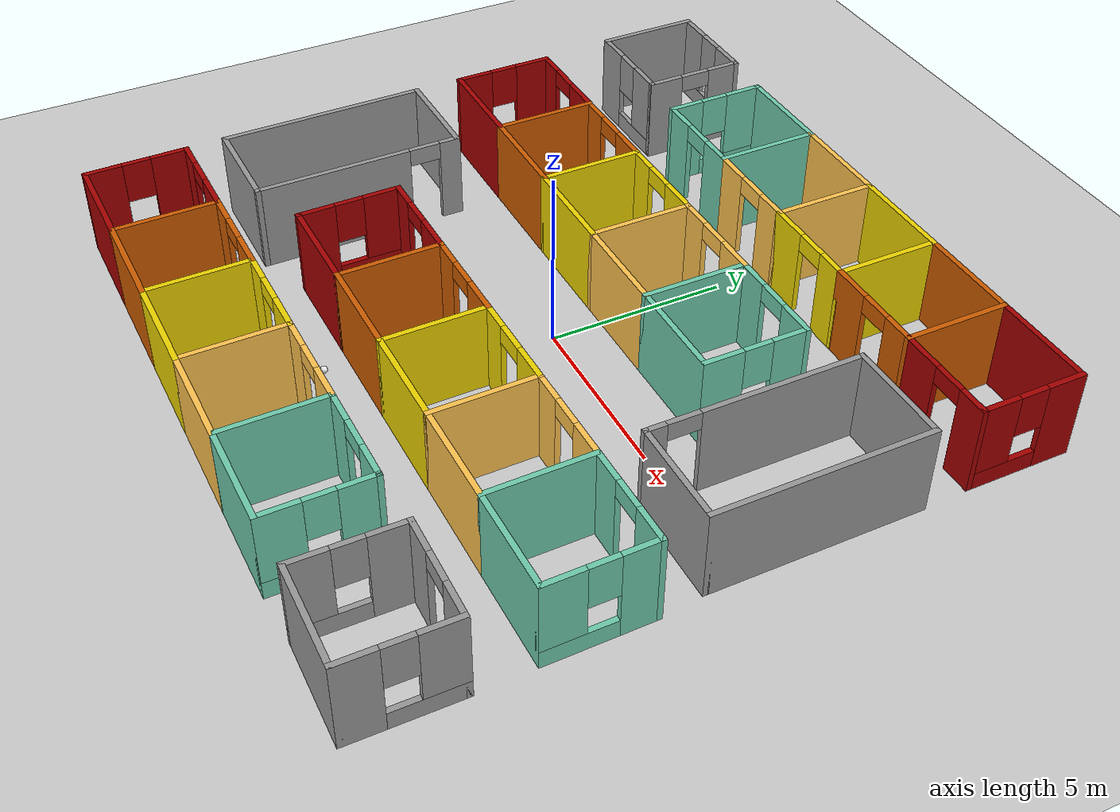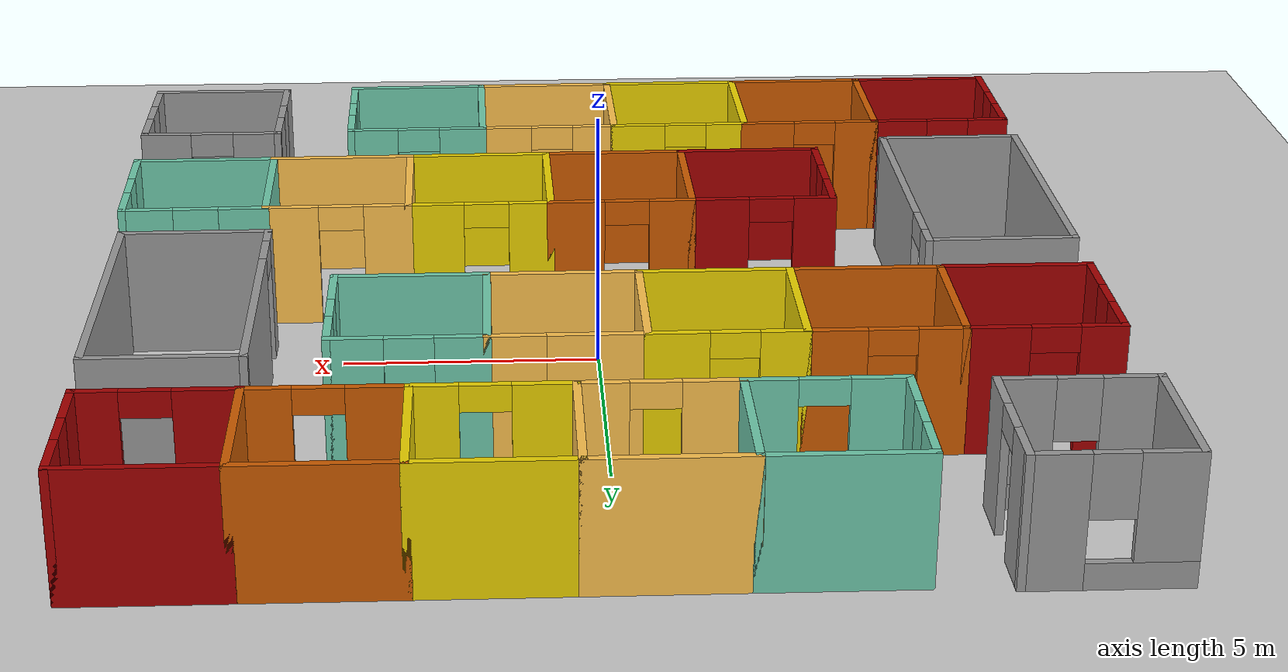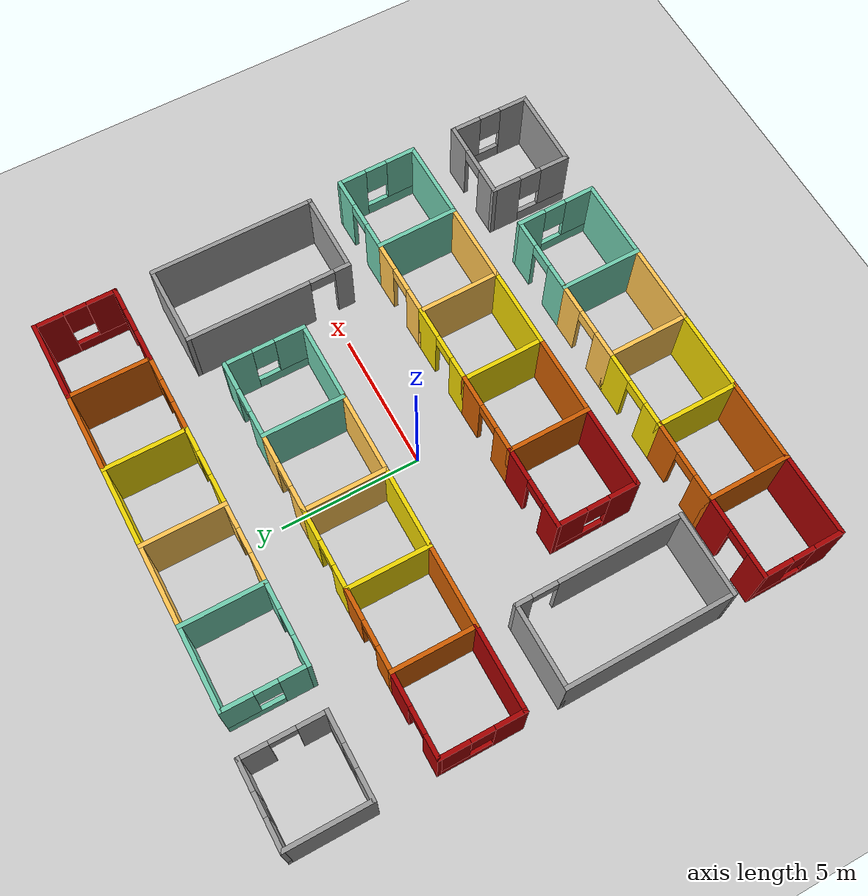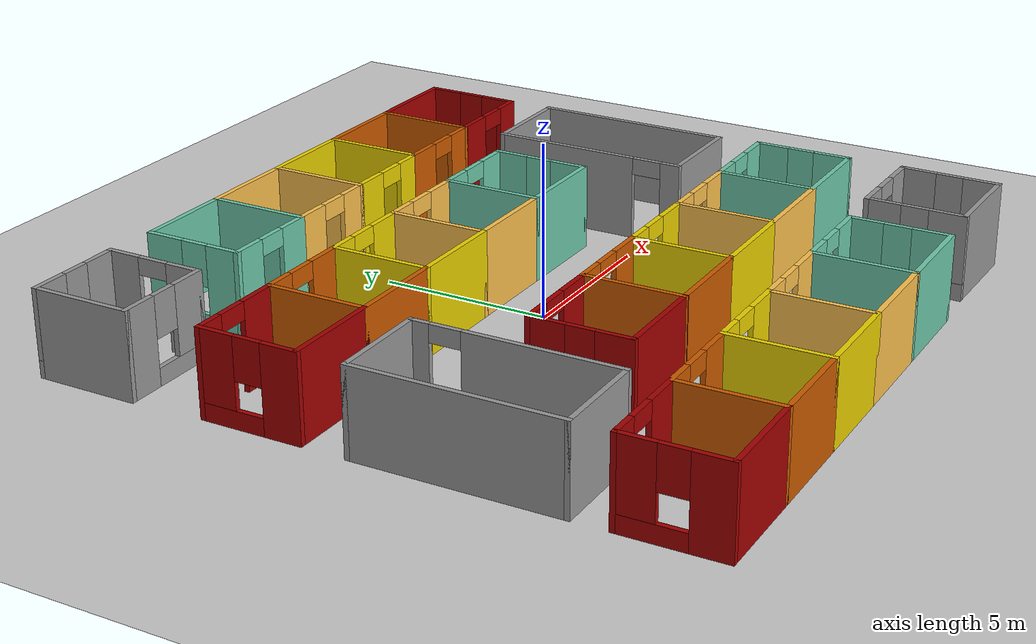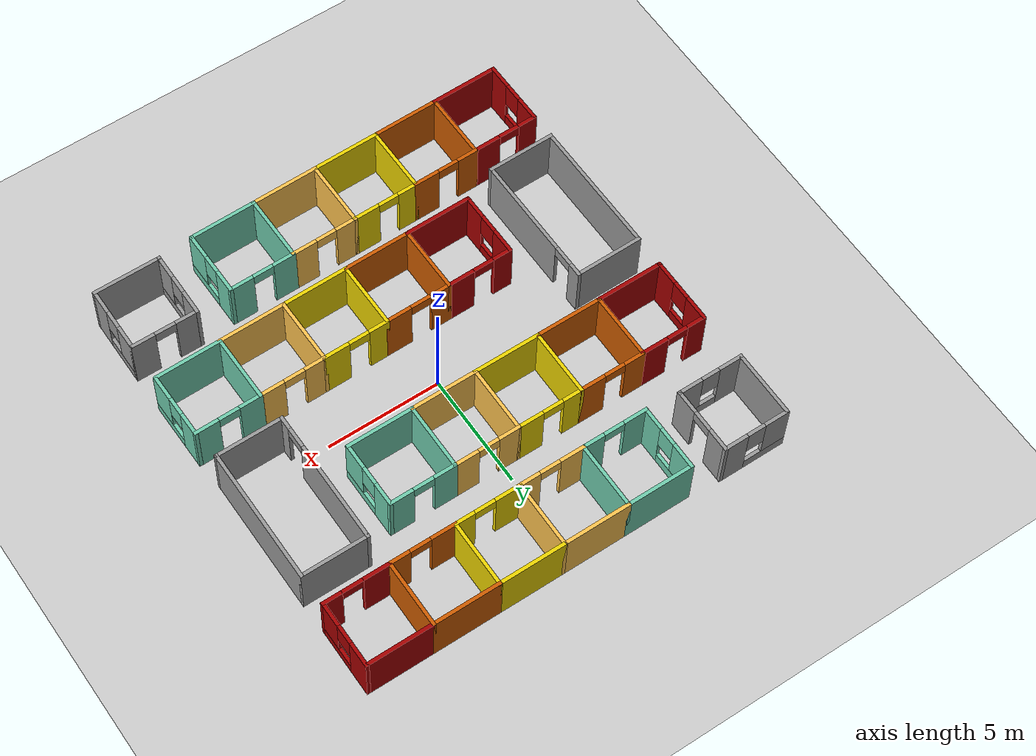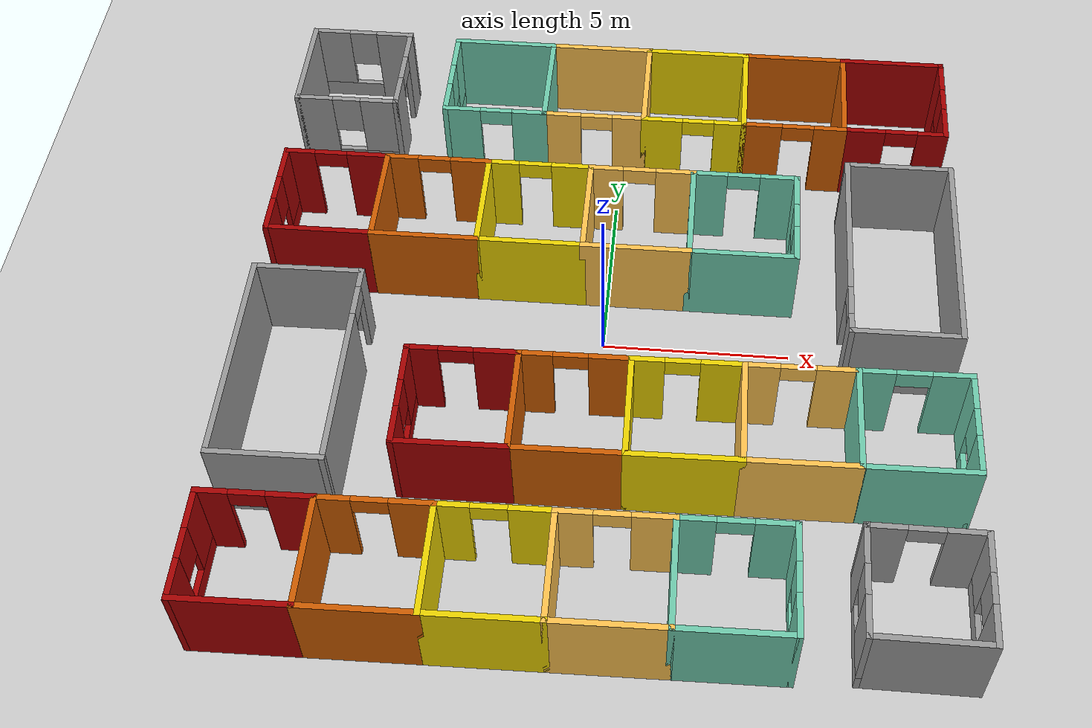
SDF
<sdf version="1.6">
 <world name="default">
  <plugin name="welcome_message" filename="libwelcome_message.so"/>
  <light name="sun" type="directional">
   <pose>0 0 10 0 -0 0</pose>
   <diffuse>0.8 0.8 0.8 1</diffuse>
   <specular>0.2 0.2 0.2 1</specular>
   <attenuation>
    <range>1000</range>
    <constant>0.9</constant>
    <linear>0.01</linear>
    <quadratic>0.001</quadratic>
   </attenuation>
   <direction>-0.5 0.1 -0.9</direction>
   <spot><inner_angle>0</inner_angle><outer_angle>0</outer_angle><falloff>0</falloff></spot>
  </light>
  <model name="ground_plane">
   <static>1</static>
   <link name="link">
    <collision name="collision">
     <geometry><plane><normal>0 0 1</normal><size>100 100</size></plane></geometry>
     <surface><friction><ode><mu>100</mu><mu2>50</mu2></ode></friction></surface>
    </collision>
    <visual name="visual">
     <cast_shadows>0</cast_shadows>
     <geometry><plane><normal>0 0 1</normal><size>100 100</size></plane></geometry>
     <material>
      <script><uri>file://media/materials/scripts/gazebo.material</uri><name>Gazebo/Grey</name></script>
     </material>
    </visual>
   </link>
  </model>
  <gravity>0 0 -9.8</gravity>
  <magnetic_field>6e-06 2.3e-05 -4.2e-05</magnetic_field>
  <atmosphere type="adiabatic"/>
  <physics name="default_physics" default="0" type="ode">
   <max_step_size>0.001</max_step_size>
   <real_time_factor>1</real_time_factor>
   <real_time_update_rate>1000</real_time_update_rate>
  </physics>
  <scene><ambient>0.4 0.4 0.4 1</ambient><background>0.7 0.7 0.7 1</background><shadows>1</shadows></scene>
  <spherical_coordinates>
   <surface_model>EARTH_WGS84</surface_model>
   <latitude_deg>0</latitude_deg>
   <longitude_deg>0</longitude_deg>
   <elevation>0</elevation>
   <heading_deg>0</heading_deg>
  </spherical_coordinates>
  <model name="office1">
   <pose>-6.56751 8.5235 0 0 -0 0</pose>
   <link name="Wall_0">
    <pose>-1.3775 -2.0475 0 0 -0 0</pose>
    <visual name="Wall_0_Visual_0">
     <pose>-0.9525 0 1.25 0 -0 0</pose>
     <geometry><box><size>1.095 0.15 2.5</size></box></geometry>
     <material>
      <script><uri>file://media/materials/scripts/gazebo.material</uri><name>Gazebo/Grey</name></script>
      <ambient>1 1 1 1</ambient>
     </material>
     <meta><layer>0</layer></meta>
    </visual>
    <collision name="Wall_0_Collision_0">
     <geometry><box><size>1.095 0.15 2.5</size></box></geometry>
     <pose>-0.9525 0 1.25 0 -0 0</pose>
    </collision>
    <visual name="Wall_0_Visual_1">
     <pose>0.5475 0 0.25 0 -0 0</pose>
     <geometry><box><size>1.905 0.15 0.5</size></box></geometry>
     <material>
      <script><uri>file://media/materials/scripts/gazebo.material</uri><name>Gazebo/Grey</name></script>
      <ambient>1 1 1 1</ambient>
     </material>
     <meta><layer>0</layer></meta>
    </visual>
    <collision name="Wall_0_Collision_1">
     <geometry><box><size>1.905 0.15 0.5</size></box></geometry>
     <pose>0.5475 0 0.25 0 -0 0</pose>
    </collision>
    <visual name="Wall_0_Visual_2">
     <pose>0.9475 0 1.5 0 -0 0</pose>
     <geometry><box><size>1.105 0.15 2</size></box></geometry>
     <material>
      <script><uri>file://media/materials/scripts/gazebo.material</uri><name>Gazebo/Grey</name></script>
      <ambient>1 1 1 1</ambient>
     </material>
     <meta><layer>0</layer></meta>
    </visual>
    <collision name="Wall_0_Collision_2">
     <geometry><box><size>1.105 0.15 2</size></box></geometry>
     <pose>0.9475 0 1.5 0 -0 0</pose>
    </collision>
    <visual name="Wall_0_Visual_3">
     <pose>-0.005 0 1.9 0 -0 0</pose>
     <geometry><box><size>0.8 0.15 1.2</size></box></geometry>
     <material>
      <script><uri>file://media/materials/scripts/gazebo.material</uri><name>Gazebo/Grey</name></script>
      <ambient>1 1 1 1</ambient>
     </material>
     <meta><layer>0</layer></meta>
    </visual>
    <collision name="Wall_0_Collision_3">
     <geometry><box><size>0.8 0.15 1.2</size></box></geometry>
     <pose>-0.005 0 1.9 0 -0 0</pose>
    </collision>
   </link>
   <link name="Wall_1">
    <pose>0.0475 -0.6225 0 0 -0 1.5708</pose>
    <visual name="Wall_1_Visual_0">
     <pose>-0.9675 0 1.25 0 -0 0</pose>
     <geometry><box><size>1.065 0.15 2.5</size></box></geometry>
     <material>
      <script><uri>file://media/materials/scripts/gazebo.material</uri><name>Gazebo/Grey</name></script>
      <ambient>1 1 1 1</ambient>
     </material>
     <meta><layer>0</layer></meta>
    </visual>
    <collision name="Wall_1_Collision_0">
     <geometry><box><size>1.065 0.15 2.5</size></box></geometry>
     <pose>-0.9675 0 1.25 0 -0 0</pose>
    </collision>
    <visual name="Wall_1_Visual_1">
     <pose>0.9825 0 1.25 0 -0 0</pose>
     <geometry><box><size>1.035 0.15 2.5</size></box></geometry>
     <material>
      <script><uri>file://media/materials/scripts/gazebo.material</uri><name>Gazebo/Grey</name></script>
      <ambient>1 1 1 1</ambient>
     </material>
     <meta><layer>0</layer></meta>
    </visual>
    <collision name="Wall_1_Collision_1">
     <geometry><box><size>1.035 0.15 2.5</size></box></geometry>
     <pose>0.9825 0 1.25 0 -0 0</pose>
    </collision>
    <visual name="Wall_1_Visual_2">
     <pose>0.015 0 2.25 0 -0 0</pose>
     <geometry><box><size>0.9 0.15 0.5</size></box></geometry>
     <material>
      <script><uri>file://media/materials/scripts/gazebo.material</uri><name>Gazebo/Grey</name></script>
      <ambient>1 1 1 1</ambient>
     </material>
     <meta><layer>0</layer></meta>
    </visual>
    <collision name="Wall_1_Collision_2">
     <geometry><box><size>0.9 0.15 0.5</size></box></geometry>
     <pose>0.015 0 2.25 0 -0 0</pose>
    </collision>
   </link>
   <link name="Wall_2">
    <pose>-1.3775 0.8025 0 0 -0 3.14159</pose>
    <visual name="Wall_2_Visual_0">
     <pose>-0.9525 0 1.25 0 -0 0</pose>
     <geometry><box><size>1.095 0.15 2.5</size></box></geometry>
     <material>
      <script><uri>file://media/materials/scripts/gazebo.material</uri><name>Gazebo/Grey</name></script>
      <ambient>1 1 1 1</ambient>
     </material>
     <meta><layer>0</layer></meta>
    </visual>
    <collision name="Wall_2_Collision_0">
     <geometry><box><size>1.095 0.15 2.5</size></box></geometry>
     <pose>-0.9525 0 1.25 0 -0 0</pose>
    </collision>
    <visual name="Wall_2_Visual_1">
     <pose>0.5475 0 0.25 0 -0 0</pose>
     <geometry><box><size>1.905 0.15 0.5</size></box></geometry>
     <material>
      <script><uri>file://media/materials/scripts/gazebo.material</uri><name>Gazebo/Grey</name></script>
      <ambient>1 1 1 1</ambient>
     </material>
     <meta><layer>0</layer></meta>
    </visual>
    <collision name="Wall_2_Collision_1">
     <geometry><box><size>1.905 0.15 0.5</size></box></geometry>
     <pose>0.5475 0 0.25 0 -0 0</pose>
    </collision>
    <visual name="Wall_2_Visual_2">
     <pose>0.9475 0 1.5 0 -0 0</pose>
     <geometry><box><size>1.105 0.15 2</size></box></geometry>
     <material>
      <script><uri>file://media/materials/scripts/gazebo.material</uri><name>Gazebo/Grey</name></script>
      <ambient>1 1 1 1</ambient>
     </material>
     <meta><layer>0</layer></meta>
    </visual>
    <collision name="Wall_2_Collision_2">
     <geometry><box><size>1.105 0.15 2</size></box></geometry>
     <pose>0.9475 0 1.5 0 -0 0</pose>
    </collision>
    <visual name="Wall_2_Visual_3">
     <pose>-0.005 0 1.9 0 -0 0</pose>
     <geometry><box><size>0.8 0.15 1.2</size></box></geometry>
     <material>
      <script><uri>file://media/materials/scripts/gazebo.material</uri><name>Gazebo/Grey</name></script>
      <ambient>1 1 1 1</ambient>
     </material>
     <meta><layer>0</layer></meta>
    </visual>
    <collision name="Wall_2_Collision_3">
     <geometry><box><size>0.8 0.15 1.2</size></box></geometry>
     <pose>-0.005 0 1.9 0 -0 0</pose>
    </collision>
   </link>
   <link name="Wall_3">
    <collision name="Wall_3_Collision">
     <geometry><box><size>3 0.15 2.5</size></box></geometry>
     <pose>0 0 1.25 0 -0 0</pose>
    </collision>
    <visual name="Wall_3_Visual">
     <pose>0 0 1.25 0 -0 0</pose>
     <geometry><box><size>3 0.15 2.5</size></box></geometry>
     <material>
      <script><uri>file://media/materials/scripts/gazebo.material</uri><name>Gazebo/Grey</name></script>
      <ambient>1 1 1 1</ambient>
     </material>
     <meta><layer>0</layer></meta>
    </visual>
    <pose>-2.8025 -0.6225 0 0 -0 -1.5708</pose>
   </link>
   <static>1</static>
  </model>
  <model name="office2_0">
   <pose>-7.13446 -2.81737 0 0 0 -1.56197</pose>
   <link name="Wall_1">
    <collision name="Wall_1_Collision">
     <geometry><box><size>6 0.15 2.5</size></box></geometry>
     <pose>0 0 1.25 0 -0 0</pose>
    </collision>
    <visual name="Wall_1_Visual">
     <pose>0 0 1.25 0 -0 0</pose>
     <geometry><box><size>6 0.15 2.5</size></box></geometry>
     <material>
      <script><uri>file://media/materials/scripts/gazebo.material</uri><name>Gazebo/Grey</name></script>
      <ambient>1 1 1 1</ambient>
     </material>
     <meta><layer>0</layer></meta>
    </visual>
    <pose>0 -2.0825 0 0 -0 0</pose>
   </link>
   <link name="Wall_2">
    <collision name="Wall_2_Collision">
     <geometry><box><size>3 0.15 2.5</size></box></geometry>
     <pose>0 0 1.25 0 -0 0</pose>
    </collision>
    <visual name="Wall_2_Visual">
     <pose>0 0 1.25 0 -0 0</pose>
     <geometry><box><size>3 0.15 2.5</size></box></geometry>
     <material>
      <script><uri>file://media/materials/scripts/gazebo.material</uri><name>Gazebo/Grey</name></script>
      <ambient>1 1 1 1</ambient>
     </material>
     <meta><layer>0</layer></meta>
    </visual>
    <pose>2.925 -0.6575 0 0 -0 1.5708</pose>
   </link>
   <link name="Wall_3">
    <pose>0 0.7675 0 0 -0 3.14159</pose>
    <visual name="Wall_3_Visual_0">
     <pose>-0.7575 0 1.25 0 -0 0</pose>
     <geometry><box><size>4.485 0.15 2.5</size></box></geometry>
     <material>
      <script><uri>file://media/materials/scripts/gazebo.material</uri><name>Gazebo/Grey</name></script>
      <ambient>1 1 1 1</ambient>
     </material>
     <meta><layer>0</layer></meta>
    </visual>
    <collision name="Wall_3_Collision_0">
     <geometry><box><size>4.485 0.15 2.5</size></box></geometry>
     <pose>-0.7575 0 1.25 0 -0 0</pose>
    </collision>
    <visual name="Wall_3_Visual_1">
     <pose>2.6925 0 1.25 0 -0 0</pose>
     <geometry><box><size>0.615 0.15 2.5</size></box></geometry>
     <material>
      <script><uri>file://media/materials/scripts/gazebo.material</uri><name>Gazebo/Grey</name></script>
      <ambient>1 1 1 1</ambient>
     </material>
     <meta><layer>0</layer></meta>
    </visual>
    <collision name="Wall_3_Collision_1">
     <geometry><box><size>0.615 0.15 2.5</size></box></geometry>
     <pose>2.6925 0 1.25 0 -0 0</pose>
    </collision>
    <visual name="Wall_3_Visual_2">
     <pose>1.935 0 2.25 0 -0 0</pose>
     <geometry><box><size>0.9 0.15 0.5</size></box></geometry>
     <material>
      <script><uri>file://media/materials/scripts/gazebo.material</uri><name>Gazebo/Grey</name></script>
      <ambient>1 1 1 1</ambient>
     </material>
     <meta><layer>0</layer></meta>
    </visual>
    <collision name="Wall_3_Collision_2">
     <geometry><box><size>0.9 0.15 0.5</size></box></geometry>
     <pose>1.935 0 2.25 0 -0 0</pose>
    </collision>
   </link>
   <link name="Wall_4">
    <collision name="Wall_4_Collision">
     <geometry><box><size>3 0.15 2.5</size></box></geometry>
     <pose>0 0 1.25 0 -0 0</pose>
    </collision>
    <visual name="Wall_4_Visual">
     <pose>0 0 1.25 0 -0 0</pose>
     <geometry><box><size>3 0.15 2.5</size></box></geometry>
     <material>
      <script><uri>file://media/materials/scripts/gazebo.material</uri><name>Gazebo/Grey</name></script>
      <ambient>1 1 1 1</ambient>
     </material>
     <meta><layer>0</layer></meta>
    </visual>
    <pose>-2.925 -0.6575 0 0 -0 -1.5708</pose>
   </link>
   <static>1</static>
  </model>
  <model name="office_4">
   <pose>2.07237 8.39329 0 0 -0 0</pose>
   <link name="Wall_0">
    <collision name="Wall_0_Collision">
     <geometry><box><size>3 0.15 2.5</size></box></geometry>
     <pose>0 0 1.25 0 -0 0</pose>
    </collision>
    <visual name="Wall_0_Visual">
     <pose>0 0 1.25 0 -0 0</pose>
     <geometry><box><size>3 0.15 2.5</size></box></geometry>
     <material>
      <script><uri>file://media/materials/scripts/gazebo.material</uri><name>Gazebo/Grey</name></script>
      <ambient>0.435294 0.796078 0.67451 1</ambient>
     </material>
     <meta><layer>0</layer></meta>
    </visual>
    <pose>-5.7 0.8025 0 0 -0 0</pose>
   </link>
   <link name="Wall_1">
    <collision name="Wall_1_Collision">
     <geometry><box><size>3 0.15 2.5</size></box></geometry>
     <pose>0 0 1.25 0 -0 0</pose>
    </collision>
    <visual name="Wall_1_Visual">
     <pose>0 0 1.25 0 -0 0</pose>
     <geometry><box><size>3 0.15 2.5</size></box></geometry>
     <material>
      <script><uri>file://media/materials/scripts/gazebo.material</uri><name>Gazebo/Grey</name></script>
      <ambient>0.435294 0.796078 0.67451 1</ambient>
     </material>
     <meta><layer>0</layer></meta>
    </visual>
    <pose>-4.275 -0.6225 0 0 -0 -1.5708</pose>
   </link>
   <link name="Wall_10">
    <pose>5.7 -2.0475 0 0 -0 3.14159</pose>
    <visual name="Wall_10_Visual_0">
     <pose>-1.06469 0 1.25 0 -0 0</pose>
     <geometry><box><size>0.870623 0.15 2.5</size></box></geometry>
     <material>
      <script><uri>file://media/materials/scripts/gazebo.material</uri><name>Gazebo/Grey</name></script>
      <ambient>0.643137 0 0 1</ambient>
     </material>
     <meta><layer>0</layer></meta>
    </visual>
    <collision name="Wall_10_Collision_0">
     <geometry><box><size>0.870623 0.15 2.5</size></box></geometry>
     <pose>-1.06469 0 1.25 0 -0 0</pose>
    </collision>
    <visual name="Wall_10_Visual_1">
     <pose>0.885312 0 1.25 0 -0 0</pose>
     <geometry><box><size>1.22938 0.15 2.5</size></box></geometry>
     <material>
      <script><uri>file://media/materials/scripts/gazebo.material</uri><name>Gazebo/Grey</name></script>
      <ambient>0.643137 0 0 1</ambient>
     </material>
     <meta><layer>0</layer></meta>
    </visual>
    <collision name="Wall_10_Collision_1">
     <geometry><box><size>1.22938 0.15 2.5</size></box></geometry>
     <pose>0.885312 0 1.25 0 -0 0</pose>
    </collision>
    <visual name="Wall_10_Visual_2">
     <pose>-0.179377 0 2.25 0 -0 0</pose>
     <geometry><box><size>0.9 0.15 0.5</size></box></geometry>
     <material>
      <script><uri>file://media/materials/scripts/gazebo.material</uri><name>Gazebo/Grey</name></script>
      <ambient>0.643137 0 0 1</ambient>
     </material>
     <meta><layer>0</layer></meta>
    </visual>
    <collision name="Wall_10_Collision_2">
     <geometry><box><size>0.9 0.15 0.5</size></box></geometry>
     <pose>-0.179377 0 2.25 0 -0 0</pose>
    </collision>
   </link>
   <link name="Wall_12">
    <pose>0 -2.0475 0 0 -0 0</pose>
    <visual name="Wall_12_Visual_0">
     <pose>-0.909766 0 1.25 0 -0 0</pose>
     <geometry><box><size>1.18047 0.15 2.5</size></box></geometry>
     <material>
      <script><uri>file://media/materials/scripts/gazebo.material</uri><name>Gazebo/Grey</name></script>
      <ambient>0.929412 0.831373 0 1</ambient>
     </material>
     <meta><layer>0</layer></meta>
    </visual>
    <collision name="Wall_12_Collision_0">
     <geometry><box><size>1.18047 0.15 2.5</size></box></geometry>
     <pose>-0.909766 0 1.25 0 -0 0</pose>
    </collision>
    <visual name="Wall_12_Visual_1">
     <pose>1.04023 0 1.25 0 -0 0</pose>
     <geometry><box><size>0.919531 0.15 2.5</size></box></geometry>
     <material>
      <script><uri>file://media/materials/scripts/gazebo.material</uri><name>Gazebo/Grey</name></script>
      <ambient>0.929412 0.831373 0 1</ambient>
     </material>
     <meta><layer>0</layer></meta>
    </visual>
    <collision name="Wall_12_Collision_1">
     <geometry><box><size>0.919531 0.15 2.5</size></box></geometry>
     <pose>1.04023 0 1.25 0 -0 0</pose>
    </collision>
    <visual name="Wall_12_Visual_2">
     <pose>0.130469 0 2.25 0 -0 0</pose>
     <geometry><box><size>0.9 0.15 0.5</size></box></geometry>
     <material>
      <script><uri>file://media/materials/scripts/gazebo.material</uri><name>Gazebo/Grey</name></script>
      <ambient>0.929412 0.831373 0 1</ambient>
     </material>
     <meta><layer>0</layer></meta>
    </visual>
    <collision name="Wall_12_Collision_2">
     <geometry><box><size>0.9 0.15 0.5</size></box></geometry>
     <pose>0.130469 0 2.25 0 -0 0</pose>
    </collision>
   </link>
   <link name="Wall_14">
    <collision name="Wall_14_Collision">
     <geometry><box><size>3 0.15 2.5</size></box></geometry>
     <pose>0 0 1.25 0 -0 0</pose>
    </collision>
    <visual name="Wall_14_Visual">
     <pose>0 0 1.25 0 -0 0</pose>
     <geometry><box><size>3 0.15 2.5</size></box></geometry>
     <material>
      <script><uri>file://media/materials/scripts/gazebo.material</uri><name>Gazebo/Grey</name></script>
      <ambient>0.807843 0.360784 0 1</ambient>
     </material>
     <meta><layer>0</layer></meta>
    </visual>
    <pose>2.85 0.8025 0 0 -0 0</pose>
   </link>
   <link name="Wall_16">
    <collision name="Wall_16_Collision">
     <geometry><box><size>3 0.15 2.5</size></box></geometry>
     <pose>0 0 1.25 0 -0 0</pose>
    </collision>
    <visual name="Wall_16_Visual">
     <pose>0 0 1.25 0 -0 0</pose>
     <geometry><box><size>3 0.15 2.5</size></box></geometry>
     <material>
      <script><uri>file://media/materials/scripts/gazebo.material</uri><name>Gazebo/Grey</name></script>
      <ambient>1 0.764706 0.305882 1</ambient>
     </material>
     <meta><layer>0</layer></meta>
    </visual>
    <pose>-2.85 0.8025 0 0 -0 0</pose>
   </link>
   <link name="Wall_18">
    <pose>-5.7 -2.0475 0 0 -0 3.14159</pose>
    <visual name="Wall_18_Visual_0">
     <pose>-0.992968 0 1.25 0 -0 0</pose>
     <geometry><box><size>1.01406 0.15 2.5</size></box></geometry>
     <material>
      <script><uri>file://media/materials/scripts/gazebo.material</uri><name>Gazebo/Grey</name></script>
      <ambient>0.435294 0.796078 0.67451 1</ambient>
     </material>
     <meta><layer>0</layer></meta>
    </visual>
    <collision name="Wall_18_Collision_0">
     <geometry><box><size>1.01406 0.15 2.5</size></box></geometry>
     <pose>-0.992968 0 1.25 0 -0 0</pose>
    </collision>
    <visual name="Wall_18_Visual_1">
     <pose>0.957032 0 1.25 0 -0 0</pose>
     <geometry><box><size>1.08594 0.15 2.5</size></box></geometry>
     <material>
      <script><uri>file://media/materials/scripts/gazebo.material</uri><name>Gazebo/Grey</name></script>
      <ambient>0.435294 0.796078 0.67451 1</ambient>
     </material>
     <meta><layer>0</layer></meta>
    </visual>
    <collision name="Wall_18_Collision_1">
     <geometry><box><size>1.08594 0.15 2.5</size></box></geometry>
     <pose>0.957032 0 1.25 0 -0 0</pose>
    </collision>
    <visual name="Wall_18_Visual_2">
     <pose>-0.035935 0 2.25 0 -0 0</pose>
     <geometry><box><size>0.9 0.15 0.5</size></box></geometry>
     <material>
      <script><uri>file://media/materials/scripts/gazebo.material</uri><name>Gazebo/Grey</name></script>
      <ambient>0.435294 0.796078 0.67451 1</ambient>
     </material>
     <meta><layer>0</layer></meta>
    </visual>
    <collision name="Wall_18_Collision_2">
     <geometry><box><size>0.9 0.15 0.5</size></box></geometry>
     <pose>-0.035935 0 2.25 0 -0 0</pose>
    </collision>
   </link>
   <link name="Wall_19">
    <pose>-7.125 -0.6225 0 0 -0 1.5708</pose>
    <visual name="Wall_19_Visual_0">
     <pose>-0.974081 0 1.25 0 -0 0</pose>
     <geometry><box><size>1.05184 0.15 2.5</size></box></geometry>
     <material>
      <script><uri>file://media/materials/scripts/gazebo.material</uri><name>Gazebo/Grey</name></script>
      <ambient>0.435294 0.796078 0.67451 1</ambient>
     </material>
     <meta><layer>0</layer></meta>
    </visual>
    <collision name="Wall_19_Collision_0">
     <geometry><box><size>1.05184 0.15 2.5</size></box></geometry>
     <pose>-0.974081 0 1.25 0 -0 0</pose>
    </collision>
    <visual name="Wall_19_Visual_1">
     <pose>0.525919 0 0.25 0 -0 0</pose>
     <geometry><box><size>1.94816 0.15 0.5</size></box></geometry>
     <material>
      <script><uri>file://media/materials/scripts/gazebo.material</uri><name>Gazebo/Grey</name></script>
      <ambient>0.435294 0.796078 0.67451 1</ambient>
     </material>
     <meta><layer>0</layer></meta>
    </visual>
    <collision name="Wall_19_Collision_1">
     <geometry><box><size>1.94816 0.15 0.5</size></box></geometry>
     <pose>0.525919 0 0.25 0 -0 0</pose>
    </collision>
    <visual name="Wall_19_Visual_2">
     <pose>0.925919 0 1.5 0 -0 0</pose>
     <geometry><box><size>1.14816 0.15 2</size></box></geometry>
     <material>
      <script><uri>file://media/materials/scripts/gazebo.material</uri><name>Gazebo/Grey</name></script>
      <ambient>0.435294 0.796078 0.67451 1</ambient>
     </material>
     <meta><layer>0</layer></meta>
    </visual>
    <collision name="Wall_19_Collision_2">
     <geometry><box><size>1.14816 0.15 2</size></box></geometry>
     <pose>0.925919 0 1.5 0 -0 0</pose>
    </collision>
    <visual name="Wall_19_Visual_3">
     <pose>-0.048161 0 1.9 0 -0 0</pose>
     <geometry><box><size>0.8 0.15 1.2</size></box></geometry>
     <material>
      <script><uri>file://media/materials/scripts/gazebo.material</uri><name>Gazebo/Grey</name></script>
      <ambient>0.435294 0.796078 0.67451 1</ambient>
     </material>
     <meta><layer>0</layer></meta>
    </visual>
    <collision name="Wall_19_Collision_3">
     <geometry><box><size>0.8 0.15 1.2</size></box></geometry>
     <pose>-0.048161 0 1.9 0 -0 0</pose>
    </collision>
   </link>
   <link name="Wall_2">
    <pose>-2.85 -2.0475 0 0 -0 0</pose>
    <visual name="Wall_2_Visual_0">
     <pose>-0.937201 0 1.25 0 -0 0</pose>
     <geometry><box><size>1.1256 0.15 2.5</size></box></geometry>
     <material>
      <script><uri>file://media/materials/scripts/gazebo.material</uri><name>Gazebo/Grey</name></script>
      <ambient>1 0.764706 0.305882 1</ambient>
     </material>
     <meta><layer>0</layer></meta>
    </visual>
    <collision name="Wall_2_Collision_0">
     <geometry><box><size>1.1256 0.15 2.5</size></box></geometry>
     <pose>-0.937201 0 1.25 0 -0 0</pose>
    </collision>
    <visual name="Wall_2_Visual_1">
     <pose>1.0128 0 1.25 0 -0 0</pose>
     <geometry><box><size>0.974402 0.15 2.5</size></box></geometry>
     <material>
      <script><uri>file://media/materials/scripts/gazebo.material</uri><name>Gazebo/Grey</name></script>
      <ambient>1 0.764706 0.305882 1</ambient>
     </material>
     <meta><layer>0</layer></meta>
    </visual>
    <collision name="Wall_2_Collision_1">
     <geometry><box><size>0.974402 0.15 2.5</size></box></geometry>
     <pose>1.0128 0 1.25 0 -0 0</pose>
    </collision>
    <visual name="Wall_2_Visual_2">
     <pose>0.075598 0 2.25 0 -0 0</pose>
     <geometry><box><size>0.9 0.15 0.5</size></box></geometry>
     <material>
      <script><uri>file://media/materials/scripts/gazebo.material</uri><name>Gazebo/Grey</name></script>
      <ambient>1 0.764706 0.305882 1</ambient>
     </material>
     <meta><layer>0</layer></meta>
    </visual>
    <collision name="Wall_2_Collision_2">
     <geometry><box><size>0.9 0.15 0.5</size></box></geometry>
     <pose>0.075598 0 2.25 0 -0 0</pose>
    </collision>
   </link>
   <link name="Wall_3">
    <collision name="Wall_3_Collision">
     <geometry><box><size>3 0.15 2.5</size></box></geometry>
     <pose>0 0 1.25 0 -0 0</pose>
    </collision>
    <visual name="Wall_3_Visual">
     <pose>0 0 1.25 0 -0 0</pose>
     <geometry><box><size>3 0.15 2.5</size></box></geometry>
     <material>
      <script><uri>file://media/materials/scripts/gazebo.material</uri><name>Gazebo/Grey</name></script>
      <ambient>1 0.764706 0.305882 1</ambient>
     </material>
     <meta><layer>0</layer></meta>
    </visual>
    <pose>-1.425 -0.6225 0 0 -0 1.5708</pose>
   </link>
   <link name="Wall_4">
    <collision name="Wall_4_Collision">
     <geometry><box><size>3 0.15 2.5</size></box></geometry>
     <pose>0 0 1.25 0 -0 0</pose>
    </collision>
    <visual name="Wall_4_Visual">
     <pose>0 0 1.25 0 -0 0</pose>
     <geometry><box><size>3 0.15 2.5</size></box></geometry>
     <material>
      <script><uri>file://media/materials/scripts/gazebo.material</uri><name>Gazebo/Grey</name></script>
      <ambient>0.929412 0.831373 0 1</ambient>
     </material>
     <meta><layer>0</layer></meta>
    </visual>
    <pose>0 0.8025 0 0 -0 0</pose>
   </link>
   <link name="Wall_5">
    <collision name="Wall_5_Collision">
     <geometry><box><size>3 0.15 2.5</size></box></geometry>
     <pose>0 0 1.25 0 -0 0</pose>
    </collision>
    <visual name="Wall_5_Visual">
     <pose>0 0 1.25 0 -0 0</pose>
     <geometry><box><size>3 0.15 2.5</size></box></geometry>
     <material>
      <script><uri>file://media/materials/scripts/gazebo.material</uri><name>Gazebo/Grey</name></script>
      <ambient>0.929412 0.831373 0 1</ambient>
     </material>
     <meta><layer>0</layer></meta>
    </visual>
    <pose>1.425 -0.6225 0 0 -0 -1.5708</pose>
   </link>
   <link name="Wall_6">
    <pose>2.85 -2.0475 0 0 -0 0</pose>
    <visual name="Wall_6_Visual_0">
     <pose>-0.920352 0 1.25 0 -0 0</pose>
     <geometry><box><size>1.1593 0.15 2.5</size></box></geometry>
     <material>
      <script><uri>file://media/materials/scripts/gazebo.material</uri><name>Gazebo/Grey</name></script>
      <ambient>0.807843 0.360784 0 1</ambient>
     </material>
     <meta><layer>0</layer></meta>
    </visual>
    <collision name="Wall_6_Collision_0">
     <geometry><box><size>1.1593 0.15 2.5</size></box></geometry>
     <pose>-0.920352 0 1.25 0 -0 0</pose>
    </collision>
    <visual name="Wall_6_Visual_1">
     <pose>1.02965 0 1.25 0 -0 0</pose>
     <geometry><box><size>0.940704 0.15 2.5</size></box></geometry>
     <material>
      <script><uri>file://media/materials/scripts/gazebo.material</uri><name>Gazebo/Grey</name></script>
      <ambient>0.807843 0.360784 0 1</ambient>
     </material>
     <meta><layer>0</layer></meta>
    </visual>
    <collision name="Wall_6_Collision_1">
     <geometry><box><size>0.940704 0.15 2.5</size></box></geometry>
     <pose>1.02965 0 1.25 0 -0 0</pose>
    </collision>
    <visual name="Wall_6_Visual_2">
     <pose>0.109296 0 2.25 0 -0 0</pose>
     <geometry><box><size>0.9 0.15 0.5</size></box></geometry>
     <material>
      <script><uri>file://media/materials/scripts/gazebo.material</uri><name>Gazebo/Grey</name></script>
      <ambient>0.807843 0.360784 0 1</ambient>
     </material>
     <meta><layer>0</layer></meta>
    </visual>
    <collision name="Wall_6_Collision_2">
     <geometry><box><size>0.9 0.15 0.5</size></box></geometry>
     <pose>0.109296 0 2.25 0 -0 0</pose>
    </collision>
   </link>
   <link name="Wall_7">
    <collision name="Wall_7_Collision">
     <geometry><box><size>3 0.15 2.5</size></box></geometry>
     <pose>0 0 1.25 0 -0 0</pose>
    </collision>
    <visual name="Wall_7_Visual">
     <pose>0 0 1.25 0 -0 0</pose>
     <geometry><box><size>3 0.15 2.5</size></box></geometry>
     <material>
      <script><uri>file://media/materials/scripts/gazebo.material</uri><name>Gazebo/Grey</name></script>
      <ambient>0.807843 0.360784 0 1</ambient>
     </material>
     <meta><layer>0</layer></meta>
    </visual>
    <pose>4.275 -0.6225 0 0 -0 1.5708</pose>
   </link>
   <link name="Wall_8">
    <collision name="Wall_8_Collision">
     <geometry><box><size>3 0.15 2.5</size></box></geometry>
     <pose>0 0 1.25 0 -0 0</pose>
    </collision>
    <visual name="Wall_8_Visual">
     <pose>0 0 1.25 0 -0 0</pose>
     <geometry><box><size>3 0.15 2.5</size></box></geometry>
     <material>
      <script><uri>file://media/materials/scripts/gazebo.material</uri><name>Gazebo/Grey</name></script>
      <ambient>0.643137 0 0 1</ambient>
     </material>
     <meta><layer>0</layer></meta>
    </visual>
    <pose>5.7 0.8025 0 0 -0 0</pose>
   </link>
   <link name="Wall_9">
    <pose>7.125 -0.6225 0 0 -0 -1.5708</pose>
    <visual name="Wall_9_Visual_0">
     <pose>-0.956337 0 1.25 0 -0 0</pose>
     <geometry><box><size>1.08733 0.15 2.5</size></box></geometry>
     <material>
      <script><uri>file://media/materials/scripts/gazebo.material</uri><name>Gazebo/Grey</name></script>
      <ambient>0.643137 0 0 1</ambient>
     </material>
     <meta><layer>0</layer></meta>
    </visual>
    <collision name="Wall_9_Collision_0">
     <geometry><box><size>1.08733 0.15 2.5</size></box></geometry>
     <pose>-0.956337 0 1.25 0 -0 0</pose>
    </collision>
    <visual name="Wall_9_Visual_1">
     <pose>0.543663 0 0.25 0 -0 0</pose>
     <geometry><box><size>1.91267 0.15 0.5</size></box></geometry>
     <material>
      <script><uri>file://media/materials/scripts/gazebo.material</uri><name>Gazebo/Grey</name></script>
      <ambient>0.643137 0 0 1</ambient>
     </material>
     <meta><layer>0</layer></meta>
    </visual>
    <collision name="Wall_9_Collision_1">
     <geometry><box><size>1.91267 0.15 0.5</size></box></geometry>
     <pose>0.543663 0 0.25 0 -0 0</pose>
    </collision>
    <visual name="Wall_9_Visual_2">
     <pose>0.943663 0 1.5 0 -0 0</pose>
     <geometry><box><size>1.11267 0.15 2</size></box></geometry>
     <material>
      <script><uri>file://media/materials/scripts/gazebo.material</uri><name>Gazebo/Grey</name></script>
      <ambient>0.643137 0 0 1</ambient>
     </material>
     <meta><layer>0</layer></meta>
    </visual>
    <collision name="Wall_9_Collision_2">
     <geometry><box><size>1.11267 0.15 2</size></box></geometry>
     <pose>0.943663 0 1.5 0 -0 0</pose>
    </collision>
    <visual name="Wall_9_Visual_3">
     <pose>-0.012674 0 1.9 0 -0 0</pose>
     <geometry><box><size>0.8 0.15 1.2</size></box></geometry>
     <material>
      <script><uri>file://media/materials/scripts/gazebo.material</uri><name>Gazebo/Grey</name></script>
      <ambient>0.643137 0 0 1</ambient>
     </material>
     <meta><layer>0</layer></meta>
    </visual>
    <collision name="Wall_9_Collision_3">
     <geometry><box><size>0.8 0.15 1.2</size></box></geometry>
     <pose>-0.012674 0 1.9 0 -0 0</pose>
    </collision>
   </link>
   <static>1</static>
  </model>
  <model name="office_4_0">
   <pose>2.32045 -4.22979 0 0 0 -3.12984</pose>
   <link name="Wall_0">
    <collision name="Wall_0_Collision">
     <geometry><box><size>3 0.15 2.5</size></box></geometry>
     <pose>0 0 1.25 0 -0 0</pose>
    </collision>
    <visual name="Wall_0_Visual">
     <pose>0 0 1.25 0 -0 0</pose>
     <geometry><box><size>3 0.15 2.5</size></box></geometry>
     <material>
      <script><uri>file://media/materials/scripts/gazebo.material</uri><name>Gazebo/Grey</name></script>
      <ambient>0.435294 0.796078 0.67451 1</ambient>
     </material>
     <meta><layer>0</layer></meta>
    </visual>
    <pose>-5.7 0.8025 0 0 -0 0</pose>
   </link>
   <link name="Wall_1">
    <collision name="Wall_1_Collision">
     <geometry><box><size>3 0.15 2.5</size></box></geometry>
     <pose>0 0 1.25 0 -0 0</pose>
    </collision>
    <visual name="Wall_1_Visual">
     <pose>0 0 1.25 0 -0 0</pose>
     <geometry><box><size>3 0.15 2.5</size></box></geometry>
     <material>
      <script><uri>file://media/materials/scripts/gazebo.material</uri><name>Gazebo/Grey</name></script>
      <ambient>0.435294 0.796078 0.67451 1</ambient>
     </material>
     <meta><layer>0</layer></meta>
    </visual>
    <pose>-4.275 -0.6225 0 0 -0 -1.5708</pose>
   </link>
   <link name="Wall_10">
    <pose>5.7 -2.0475 0 0 -0 3.14159</pose>
    <visual name="Wall_10_Visual_0">
     <pose>-1.06469 0 1.25 0 -0 0</pose>
     <geometry><box><size>0.870623 0.15 2.5</size></box></geometry>
     <material>
      <script><uri>file://media/materials/scripts/gazebo.material</uri><name>Gazebo/Grey</name></script>
      <ambient>0.643137 0 0 1</ambient>
     </material>
     <meta><layer>0</layer></meta>
    </visual>
    <collision name="Wall_10_Collision_0">
     <geometry><box><size>0.870623 0.15 2.5</size></box></geometry>
     <pose>-1.06469 0 1.25 0 -0 0</pose>
    </collision>
    <visual name="Wall_10_Visual_1">
     <pose>0.885312 0 1.25 0 -0 0</pose>
     <geometry><box><size>1.22938 0.15 2.5</size></box></geometry>
     <material>
      <script><uri>file://media/materials/scripts/gazebo.material</uri><name>Gazebo/Grey</name></script>
      <ambient>0.643137 0 0 1</ambient>
     </material>
     <meta><layer>0</layer></meta>
    </visual>
    <collision name="Wall_10_Collision_1">
     <geometry><box><size>1.22938 0.15 2.5</size></box></geometry>
     <pose>0.885312 0 1.25 0 -0 0</pose>
    </collision>
    <visual name="Wall_10_Visual_2">
     <pose>-0.179377 0 2.25 0 -0 0</pose>
     <geometry><box><size>0.9 0.15 0.5</size></box></geometry>
     <material>
      <script><uri>file://media/materials/scripts/gazebo.material</uri><name>Gazebo/Grey</name></script>
      <ambient>0.643137 0 0 1</ambient>
     </material>
     <meta><layer>0</layer></meta>
    </visual>
    <collision name="Wall_10_Collision_2">
     <geometry><box><size>0.9 0.15 0.5</size></box></geometry>
     <pose>-0.179377 0 2.25 0 -0 0</pose>
    </collision>
   </link>
   <link name="Wall_12">
    <pose>0 -2.0475 0 0 -0 0</pose>
    <visual name="Wall_12_Visual_0">
     <pose>-0.909766 0 1.25 0 -0 0</pose>
     <geometry><box><size>1.18047 0.15 2.5</size></box></geometry>
     <material>
      <script><uri>file://media/materials/scripts/gazebo.material</uri><name>Gazebo/Grey</name></script>
      <ambient>0.929412 0.831373 0 1</ambient>
     </material>
     <meta><layer>0</layer></meta>
    </visual>
    <collision name="Wall_12_Collision_0">
     <geometry><box><size>1.18047 0.15 2.5</size></box></geometry>
     <pose>-0.909766 0 1.25 0 -0 0</pose>
    </collision>
    <visual name="Wall_12_Visual_1">
     <pose>1.04023 0 1.25 0 -0 0</pose>
     <geometry><box><size>0.919531 0.15 2.5</size></box></geometry>
     <material>
      <script><uri>file://media/materials/scripts/gazebo.material</uri><name>Gazebo/Grey</name></script>
      <ambient>0.929412 0.831373 0 1</ambient>
     </material>
     <meta><layer>0</layer></meta>
    </visual>
    <collision name="Wall_12_Collision_1">
     <geometry><box><size>0.919531 0.15 2.5</size></box></geometry>
     <pose>1.04023 0 1.25 0 -0 0</pose>
    </collision>
    <visual name="Wall_12_Visual_2">
     <pose>0.130469 0 2.25 0 -0 0</pose>
     <geometry><box><size>0.9 0.15 0.5</size></box></geometry>
     <material>
      <script><uri>file://media/materials/scripts/gazebo.material</uri><name>Gazebo/Grey</name></script>
      <ambient>0.929412 0.831373 0 1</ambient>
     </material>
     <meta><layer>0</layer></meta>
    </visual>
    <collision name="Wall_12_Collision_2">
     <geometry><box><size>0.9 0.15 0.5</size></box></geometry>
     <pose>0.130469 0 2.25 0 -0 0</pose>
    </collision>
   </link>
   <link name="Wall_14">
    <collision name="Wall_14_Collision">
     <geometry><box><size>3 0.15 2.5</size></box></geometry>
     <pose>0 0 1.25 0 -0 0</pose>
    </collision>
    <visual name="Wall_14_Visual">
     <pose>0 0 1.25 0 -0 0</pose>
     <geometry><box><size>3 0.15 2.5</size></box></geometry>
     <material>
      <script><uri>file://media/materials/scripts/gazebo.material</uri><name>Gazebo/Grey</name></script>
      <ambient>0.807843 0.360784 0 1</ambient>
     </material>
     <meta><layer>0</layer></meta>
    </visual>
    <pose>2.85 0.8025 0 0 -0 0</pose>
   </link>
   <link name="Wall_16">
    <collision name="Wall_16_Collision">
     <geometry><box><size>3 0.15 2.5</size></box></geometry>
     <pose>0 0 1.25 0 -0 0</pose>
    </collision>
    <visual name="Wall_16_Visual">
     <pose>0 0 1.25 0 -0 0</pose>
     <geometry><box><size>3 0.15 2.5</size></box></geometry>
     <material>
      <script><uri>file://media/materials/scripts/gazebo.material</uri><name>Gazebo/Grey</name></script>
      <ambient>1 0.764706 0.305882 1</ambient>
     </material>
     <meta><layer>0</layer></meta>
    </visual>
    <pose>-2.85 0.8025 0 0 -0 0</pose>
   </link>
   <link name="Wall_18">
    <pose>-5.7 -2.0475 0 0 -0 3.14159</pose>
    <visual name="Wall_18_Visual_0">
     <pose>-0.992968 0 1.25 0 -0 0</pose>
     <geometry><box><size>1.01406 0.15 2.5</size></box></geometry>
     <material>
      <script><uri>file://media/materials/scripts/gazebo.material</uri><name>Gazebo/Grey</name></script>
      <ambient>0.435294 0.796078 0.67451 1</ambient>
     </material>
     <meta><layer>0</layer></meta>
    </visual>
    <collision name="Wall_18_Collision_0">
     <geometry><box><size>1.01406 0.15 2.5</size></box></geometry>
     <pose>-0.992968 0 1.25 0 -0 0</pose>
    </collision>
    <visual name="Wall_18_Visual_1">
     <pose>0.957032 0 1.25 0 -0 0</pose>
     <geometry><box><size>1.08594 0.15 2.5</size></box></geometry>
     <material>
      <script><uri>file://media/materials/scripts/gazebo.material</uri><name>Gazebo/Grey</name></script>
      <ambient>0.435294 0.796078 0.67451 1</ambient>
     </material>
     <meta><layer>0</layer></meta>
    </visual>
    <collision name="Wall_18_Collision_1">
     <geometry><box><size>1.08594 0.15 2.5</size></box></geometry>
     <pose>0.957032 0 1.25 0 -0 0</pose>
    </collision>
    <visual name="Wall_18_Visual_2">
     <pose>-0.035935 0 2.25 0 -0 0</pose>
     <geometry><box><size>0.9 0.15 0.5</size></box></geometry>
     <material>
      <script><uri>file://media/materials/scripts/gazebo.material</uri><name>Gazebo/Grey</name></script>
      <ambient>0.435294 0.796078 0.67451 1</ambient>
     </material>
     <meta><layer>0</layer></meta>
    </visual>
    <collision name="Wall_18_Collision_2">
     <geometry><box><size>0.9 0.15 0.5</size></box></geometry>
     <pose>-0.035935 0 2.25 0 -0 0</pose>
    </collision>
   </link>
   <link name="Wall_19">
    <pose>-7.125 -0.6225 0 0 -0 1.5708</pose>
    <visual name="Wall_19_Visual_0">
     <pose>-0.974081 0 1.25 0 -0 0</pose>
     <geometry><box><size>1.05184 0.15 2.5</size></box></geometry>
     <material>
      <script><uri>file://media/materials/scripts/gazebo.material</uri><name>Gazebo/Grey</name></script>
      <ambient>0.435294 0.796078 0.67451 1</ambient>
     </material>
     <meta><layer>0</layer></meta>
    </visual>
    <collision name="Wall_19_Collision_0">
     <geometry><box><size>1.05184 0.15 2.5</size></box></geometry>
     <pose>-0.974081 0 1.25 0 -0 0</pose>
    </collision>
    <visual name="Wall_19_Visual_1">
     <pose>0.525919 0 0.25 0 -0 0</pose>
     <geometry><box><size>1.94816 0.15 0.5</size></box></geometry>
     <material>
      <script><uri>file://media/materials/scripts/gazebo.material</uri><name>Gazebo/Grey</name></script>
      <ambient>0.435294 0.796078 0.67451 1</ambient>
     </material>
     <meta><layer>0</layer></meta>
    </visual>
    <collision name="Wall_19_Collision_1">
     <geometry><box><size>1.94816 0.15 0.5</size></box></geometry>
     <pose>0.525919 0 0.25 0 -0 0</pose>
    </collision>
    <visual name="Wall_19_Visual_2">
     <pose>0.925919 0 1.5 0 -0 0</pose>
     <geometry><box><size>1.14816 0.15 2</size></box></geometry>
     <material>
      <script><uri>file://media/materials/scripts/gazebo.material</uri><name>Gazebo/Grey</name></script>
      <ambient>0.435294 0.796078 0.67451 1</ambient>
     </material>
     <meta><layer>0</layer></meta>
    </visual>
    <collision name="Wall_19_Collision_2">
     <geometry><box><size>1.14816 0.15 2</size></box></geometry>
     <pose>0.925919 0 1.5 0 -0 0</pose>
    </collision>
    <visual name="Wall_19_Visual_3">
     <pose>-0.048161 0 1.9 0 -0 0</pose>
     <geometry><box><size>0.8 0.15 1.2</size></box></geometry>
     <material>
      <script><uri>file://media/materials/scripts/gazebo.material</uri><name>Gazebo/Grey</name></script>
      <ambient>0.435294 0.796078 0.67451 1</ambient>
     </material>
     <meta><layer>0</layer></meta>
    </visual>
    <collision name="Wall_19_Collision_3">
     <geometry><box><size>0.8 0.15 1.2</size></box></geometry>
     <pose>-0.048161 0 1.9 0 -0 0</pose>
    </collision>
   </link>
   <link name="Wall_2">
    <pose>-2.85 -2.0475 0 0 -0 0</pose>
    <visual name="Wall_2_Visual_0">
     <pose>-0.937201 0 1.25 0 -0 0</pose>
     <geometry><box><size>1.1256 0.15 2.5</size></box></geometry>
     <material>
      <script><uri>file://media/materials/scripts/gazebo.material</uri><name>Gazebo/Grey</name></script>
      <ambient>1 0.764706 0.305882 1</ambient>
     </material>
     <meta><layer>0</layer></meta>
    </visual>
    <collision name="Wall_2_Collision_0">
     <geometry><box><size>1.1256 0.15 2.5</size></box></geometry>
     <pose>-0.937201 0 1.25 0 -0 0</pose>
    </collision>
    <visual name="Wall_2_Visual_1">
     <pose>1.0128 0 1.25 0 -0 0</pose>
     <geometry><box><size>0.974402 0.15 2.5</size></box></geometry>
     <material>
      <script><uri>file://media/materials/scripts/gazebo.material</uri><name>Gazebo/Grey</name></script>
      <ambient>1 0.764706 0.305882 1</ambient>
     </material>
     <meta><layer>0</layer></meta>
    </visual>
    <collision name="Wall_2_Collision_1">
     <geometry><box><size>0.974402 0.15 2.5</size></box></geometry>
     <pose>1.0128 0 1.25 0 -0 0</pose>
    </collision>
    <visual name="Wall_2_Visual_2">
     <pose>0.075598 0 2.25 0 -0 0</pose>
     <geometry><box><size>0.9 0.15 0.5</size></box></geometry>
     <material>
      <script><uri>file://media/materials/scripts/gazebo.material</uri><name>Gazebo/Grey</name></script>
      <ambient>1 0.764706 0.305882 1</ambient>
     </material>
     <meta><layer>0</layer></meta>
    </visual>
    <collision name="Wall_2_Collision_2">
     <geometry><box><size>0.9 0.15 0.5</size></box></geometry>
     <pose>0.075598 0 2.25 0 -0 0</pose>
    </collision>
   </link>
   <link name="Wall_3">
    <collision name="Wall_3_Collision">
     <geometry><box><size>3 0.15 2.5</size></box></geometry>
     <pose>0 0 1.25 0 -0 0</pose>
    </collision>
    <visual name="Wall_3_Visual">
     <pose>0 0 1.25 0 -0 0</pose>
     <geometry><box><size>3 0.15 2.5</size></box></geometry>
     <material>
      <script><uri>file://media/materials/scripts/gazebo.material</uri><name>Gazebo/Grey</name></script>
      <ambient>1 0.764706 0.305882 1</ambient>
     </material>
     <meta><layer>0</layer></meta>
    </visual>
    <pose>-1.425 -0.6225 0 0 -0 1.5708</pose>
   </link>
   <link name="Wall_4">
    <collision name="Wall_4_Collision">
     <geometry><box><size>3 0.15 2.5</size></box></geometry>
     <pose>0 0 1.25 0 -0 0</pose>
    </collision>
    <visual name="Wall_4_Visual">
     <pose>0 0 1.25 0 -0 0</pose>
     <geometry><box><size>3 0.15 2.5</size></box></geometry>
     <material>
      <script><uri>file://media/materials/scripts/gazebo.material</uri><name>Gazebo/Grey</name></script>
      <ambient>0.929412 0.831373 0 1</ambient>
     </material>
     <meta><layer>0</layer></meta>
    </visual>
    <pose>0 0.8025 0 0 -0 0</pose>
   </link>
   <link name="Wall_5">
    <collision name="Wall_5_Collision">
     <geometry><box><size>3 0.15 2.5</size></box></geometry>
     <pose>0 0 1.25 0 -0 0</pose>
    </collision>
    <visual name="Wall_5_Visual">
     <pose>0 0 1.25 0 -0 0</pose>
     <geometry><box><size>3 0.15 2.5</size></box></geometry>
     <material>
      <script><uri>file://media/materials/scripts/gazebo.material</uri><name>Gazebo/Grey</name></script>
      <ambient>0.929412 0.831373 0 1</ambient>
     </material>
     <meta><layer>0</layer></meta>
    </visual>
    <pose>1.425 -0.6225 0 0 -0 -1.5708</pose>
   </link>
   <link name="Wall_6">
    <pose>2.85 -2.0475 0 0 -0 0</pose>
    <visual name="Wall_6_Visual_0">
     <pose>-0.920352 0 1.25 0 -0 0</pose>
     <geometry><box><size>1.1593 0.15 2.5</size></box></geometry>
     <material>
      <script><uri>file://media/materials/scripts/gazebo.material</uri><name>Gazebo/Grey</name></script>
      <ambient>0.807843 0.360784 0 1</ambient>
     </material>
     <meta><layer>0</layer></meta>
    </visual>
    <collision name="Wall_6_Collision_0">
     <geometry><box><size>1.1593 0.15 2.5</size></box></geometry>
     <pose>-0.920352 0 1.25 0 -0 0</pose>
    </collision>
    <visual name="Wall_6_Visual_1">
     <pose>1.02965 0 1.25 0 -0 0</pose>
     <geometry><box><size>0.940704 0.15 2.5</size></box></geometry>
     <material>
      <script><uri>file://media/materials/scripts/gazebo.material</uri><name>Gazebo/Grey</name></script>
      <ambient>0.807843 0.360784 0 1</ambient>
     </material>
     <meta><layer>0</layer></meta>
    </visual>
    <collision name="Wall_6_Collision_1">
     <geometry><box><size>0.940704 0.15 2.5</size></box></geometry>
     <pose>1.02965 0 1.25 0 -0 0</pose>
    </collision>
    <visual name="Wall_6_Visual_2">
     <pose>0.109296 0 2.25 0 -0 0</pose>
     <geometry><box><size>0.9 0.15 0.5</size></box></geometry>
     <material>
      <script><uri>file://media/materials/scripts/gazebo.material</uri><name>Gazebo/Grey</name></script>
      <ambient>0.807843 0.360784 0 1</ambient>
     </material>
     <meta><layer>0</layer></meta>
    </visual>
    <collision name="Wall_6_Collision_2">
     <geometry><box><size>0.9 0.15 0.5</size></box></geometry>
     <pose>0.109296 0 2.25 0 -0 0</pose>
    </collision>
   </link>
   <link name="Wall_7">
    <collision name="Wall_7_Collision">
     <geometry><box><size>3 0.15 2.5</size></box></geometry>
     <pose>0 0 1.25 0 -0 0</pose>
    </collision>
    <visual name="Wall_7_Visual">
     <pose>0 0 1.25 0 -0 0</pose>
     <geometry><box><size>3 0.15 2.5</size></box></geometry>
     <material>
      <script><uri>file://media/materials/scripts/gazebo.material</uri><name>Gazebo/Grey</name></script>
      <ambient>0.807843 0.360784 0 1</ambient>
     </material>
     <meta><layer>0</layer></meta>
    </visual>
    <pose>4.275 -0.6225 0 0 -0 1.5708</pose>
   </link>
   <link name="Wall_8">
    <collision name="Wall_8_Collision">
     <geometry><box><size>3 0.15 2.5</size></box></geometry>
     <pose>0 0 1.25 0 -0 0</pose>
    </collision>
    <visual name="Wall_8_Visual">
     <pose>0 0 1.25 0 -0 0</pose>
     <geometry><box><size>3 0.15 2.5</size></box></geometry>
     <material>
      <script><uri>file://media/materials/scripts/gazebo.material</uri><name>Gazebo/Grey</name></script>
      <ambient>0.643137 0 0 1</ambient>
     </material>
     <meta><layer>0</layer></meta>
    </visual>
    <pose>5.7 0.8025 0 0 -0 0</pose>
   </link>
   <link name="Wall_9">
    <pose>7.125 -0.6225 0 0 -0 -1.5708</pose>
    <visual name="Wall_9_Visual_0">
     <pose>-0.956337 0 1.25 0 -0 0</pose>
     <geometry><box><size>1.08733 0.15 2.5</size></box></geometry>
     <material>
      <script><uri>file://media/materials/scripts/gazebo.material</uri><name>Gazebo/Grey</name></script>
      <ambient>0.643137 0 0 1</ambient>
     </material>
     <meta><layer>0</layer></meta>
    </visual>
    <collision name="Wall_9_Collision_0">
     <geometry><box><size>1.08733 0.15 2.5</size></box></geometry>
     <pose>-0.956337 0 1.25 0 -0 0</pose>
    </collision>
    <visual name="Wall_9_Visual_1">
     <pose>0.543663 0 0.25 0 -0 0</pose>
     <geometry><box><size>1.91267 0.15 0.5</size></box></geometry>
     <material>
      <script><uri>file://media/materials/scripts/gazebo.material</uri><name>Gazebo/Grey</name></script>
      <ambient>0.643137 0 0 1</ambient>
     </material>
     <meta><layer>0</layer></meta>
    </visual>
    <collision name="Wall_9_Collision_1">
     <geometry><box><size>1.91267 0.15 0.5</size></box></geometry>
     <pose>0.543663 0 0.25 0 -0 0</pose>
    </collision>
    <visual name="Wall_9_Visual_2">
     <pose>0.943663 0 1.5 0 -0 0</pose>
     <geometry><box><size>1.11267 0.15 2</size></box></geometry>
     <material>
      <script><uri>file://media/materials/scripts/gazebo.material</uri><name>Gazebo/Grey</name></script>
      <ambient>0.643137 0 0 1</ambient>
     </material>
     <meta><layer>0</layer></meta>
    </visual>
    <collision name="Wall_9_Collision_2">
     <geometry><box><size>1.11267 0.15 2</size></box></geometry>
     <pose>0.943663 0 1.5 0 -0 0</pose>
    </collision>
    <visual name="Wall_9_Visual_3">
     <pose>-0.012674 0 1.9 0 -0 0</pose>
     <geometry><box><size>0.8 0.15 1.2</size></box></geometry>
     <material>
      <script><uri>file://media/materials/scripts/gazebo.material</uri><name>Gazebo/Grey</name></script>
      <ambient>0.643137 0 0 1</ambient>
     </material>
     <meta><layer>0</layer></meta>
    </visual>
    <collision name="Wall_9_Collision_3">
     <geometry><box><size>0.8 0.15 1.2</size></box></geometry>
     <pose>-0.012674 0 1.9 0 -0 0</pose>
    </collision>
   </link>
   <static>1</static>
  </model>
  <model name="office_4_1">
   <pose>-2.11062 2.2821 0 0 -0 -3.14021</pose>
   <link name="Wall_0">
    <collision name="Wall_0_Collision">
     <geometry><box><size>3 0.15 2.5</size></box></geometry>
     <pose>0 0 1.25 0 -0 0</pose>
    </collision>
    <visual name="Wall_0_Visual">
     <pose>0 0 1.25 0 -0 0</pose>
     <geometry><box><size>3 0.15 2.5</size></box></geometry>
     <material>
      <script><uri>file://media/materials/scripts/gazebo.material</uri><name>Gazebo/Grey</name></script>
      <ambient>0.435294 0.796078 0.67451 1</ambient>
     </material>
     <meta><layer>0</layer></meta>
    </visual>
    <pose>-5.7 0.8025 0 0 -0 0</pose>
   </link>
   <link name="Wall_1">
    <collision name="Wall_1_Collision">
     <geometry><box><size>3 0.15 2.5</size></box></geometry>
     <pose>0 0 1.25 0 -0 0</pose>
    </collision>
    <visual name="Wall_1_Visual">
     <pose>0 0 1.25 0 -0 0</pose>
     <geometry><box><size>3 0.15 2.5</size></box></geometry>
     <material>
      <script><uri>file://media/materials/scripts/gazebo.material</uri><name>Gazebo/Grey</name></script>
      <ambient>0.435294 0.796078 0.67451 1</ambient>
     </material>
     <meta><layer>0</layer></meta>
    </visual>
    <pose>-4.275 -0.6225 0 0 -0 -1.5708</pose>
   </link>
   <link name="Wall_10">
    <pose>5.7 -2.0475 0 0 -0 3.14159</pose>
    <visual name="Wall_10_Visual_0">
     <pose>-1.06469 0 1.25 0 -0 0</pose>
     <geometry><box><size>0.870623 0.15 2.5</size></box></geometry>
     <material>
      <script><uri>file://media/materials/scripts/gazebo.material</uri><name>Gazebo/Grey</name></script>
      <ambient>0.643137 0 0 1</ambient>
     </material>
     <meta><layer>0</layer></meta>
    </visual>
    <collision name="Wall_10_Collision_0">
     <geometry><box><size>0.870623 0.15 2.5</size></box></geometry>
     <pose>-1.06469 0 1.25 0 -0 0</pose>
    </collision>
    <visual name="Wall_10_Visual_1">
     <pose>0.885312 0 1.25 0 -0 0</pose>
     <geometry><box><size>1.22938 0.15 2.5</size></box></geometry>
     <material>
      <script><uri>file://media/materials/scripts/gazebo.material</uri><name>Gazebo/Grey</name></script>
      <ambient>0.643137 0 0 1</ambient>
     </material>
     <meta><layer>0</layer></meta>
    </visual>
    <collision name="Wall_10_Collision_1">
     <geometry><box><size>1.22938 0.15 2.5</size></box></geometry>
     <pose>0.885312 0 1.25 0 -0 0</pose>
    </collision>
    <visual name="Wall_10_Visual_2">
     <pose>-0.179377 0 2.25 0 -0 0</pose>
     <geometry><box><size>0.9 0.15 0.5</size></box></geometry>
     <material>
      <script><uri>file://media/materials/scripts/gazebo.material</uri><name>Gazebo/Grey</name></script>
      <ambient>0.643137 0 0 1</ambient>
     </material>
     <meta><layer>0</layer></meta>
    </visual>
    <collision name="Wall_10_Collision_2">
     <geometry><box><size>0.9 0.15 0.5</size></box></geometry>
     <pose>-0.179377 0 2.25 0 -0 0</pose>
    </collision>
   </link>
   <link name="Wall_12">
    <pose>0 -2.0475 0 0 -0 0</pose>
    <visual name="Wall_12_Visual_0">
     <pose>-0.909766 0 1.25 0 -0 0</pose>
     <geometry><box><size>1.18047 0.15 2.5</size></box></geometry>
     <material>
      <script><uri>file://media/materials/scripts/gazebo.material</uri><name>Gazebo/Grey</name></script>
      <ambient>0.929412 0.831373 0 1</ambient>
     </material>
     <meta><layer>0</layer></meta>
    </visual>
    <collision name="Wall_12_Collision_0">
     <geometry><box><size>1.18047 0.15 2.5</size></box></geometry>
     <pose>-0.909766 0 1.25 0 -0 0</pose>
    </collision>
    <visual name="Wall_12_Visual_1">
     <pose>1.04023 0 1.25 0 -0 0</pose>
     <geometry><box><size>0.919531 0.15 2.5</size></box></geometry>
     <material>
      <script><uri>file://media/materials/scripts/gazebo.material</uri><name>Gazebo/Grey</name></script>
      <ambient>0.929412 0.831373 0 1</ambient>
     </material>
     <meta><layer>0</layer></meta>
    </visual>
    <collision name="Wall_12_Collision_1">
     <geometry><box><size>0.919531 0.15 2.5</size></box></geometry>
     <pose>1.04023 0 1.25 0 -0 0</pose>
    </collision>
    <visual name="Wall_12_Visual_2">
     <pose>0.130469 0 2.25 0 -0 0</pose>
     <geometry><box><size>0.9 0.15 0.5</size></box></geometry>
     <material>
      <script><uri>file://media/materials/scripts/gazebo.material</uri><name>Gazebo/Grey</name></script>
      <ambient>0.929412 0.831373 0 1</ambient>
     </material>
     <meta><layer>0</layer></meta>
    </visual>
    <collision name="Wall_12_Collision_2">
     <geometry><box><size>0.9 0.15 0.5</size></box></geometry>
     <pose>0.130469 0 2.25 0 -0 0</pose>
    </collision>
   </link>
   <link name="Wall_14">
    <collision name="Wall_14_Collision">
     <geometry><box><size>3 0.15 2.5</size></box></geometry>
     <pose>0 0 1.25 0 -0 0</pose>
    </collision>
    <visual name="Wall_14_Visual">
     <pose>0 0 1.25 0 -0 0</pose>
     <geometry><box><size>3 0.15 2.5</size></box></geometry>
     <material>
      <script><uri>file://media/materials/scripts/gazebo.material</uri><name>Gazebo/Grey</name></script>
      <ambient>0.807843 0.360784 0 1</ambient>
     </material>
     <meta><layer>0</layer></meta>
    </visual>
    <pose>2.85 0.8025 0 0 -0 0</pose>
   </link>
   <link name="Wall_16">
    <collision name="Wall_16_Collision">
     <geometry><box><size>3 0.15 2.5</size></box></geometry>
     <pose>0 0 1.25 0 -0 0</pose>
    </collision>
    <visual name="Wall_16_Visual">
     <pose>0 0 1.25 0 -0 0</pose>
     <geometry><box><size>3 0.15 2.5</size></box></geometry>
     <material>
      <script><uri>file://media/materials/scripts/gazebo.material</uri><name>Gazebo/Grey</name></script>
      <ambient>1 0.764706 0.305882 1</ambient>
     </material>
     <meta><layer>0</layer></meta>
    </visual>
    <pose>-2.85 0.8025 0 0 -0 0</pose>
   </link>
   <link name="Wall_18">
    <pose>-5.7 -2.0475 0 0 -0 3.14159</pose>
    <visual name="Wall_18_Visual_0">
     <pose>-0.992968 0 1.25 0 -0 0</pose>
     <geometry><box><size>1.01406 0.15 2.5</size></box></geometry>
     <material>
      <script><uri>file://media/materials/scripts/gazebo.material</uri><name>Gazebo/Grey</name></script>
      <ambient>0.435294 0.796078 0.67451 1</ambient>
     </material>
     <meta><layer>0</layer></meta>
    </visual>
    <collision name="Wall_18_Collision_0">
     <geometry><box><size>1.01406 0.15 2.5</size></box></geometry>
     <pose>-0.992968 0 1.25 0 -0 0</pose>
    </collision>
    <visual name="Wall_18_Visual_1">
     <pose>0.957032 0 1.25 0 -0 0</pose>
     <geometry><box><size>1.08594 0.15 2.5</size></box></geometry>
     <material>
      <script><uri>file://media/materials/scripts/gazebo.material</uri><name>Gazebo/Grey</name></script>
      <ambient>0.435294 0.796078 0.67451 1</ambient>
     </material>
     <meta><layer>0</layer></meta>
    </visual>
    <collision name="Wall_18_Collision_1">
     <geometry><box><size>1.08594 0.15 2.5</size></box></geometry>
     <pose>0.957032 0 1.25 0 -0 0</pose>
    </collision>
    <visual name="Wall_18_Visual_2">
     <pose>-0.035935 0 2.25 0 -0 0</pose>
     <geometry><box><size>0.9 0.15 0.5</size></box></geometry>
     <material>
      <script><uri>file://media/materials/scripts/gazebo.material</uri><name>Gazebo/Grey</name></script>
      <ambient>0.435294 0.796078 0.67451 1</ambient>
     </material>
     <meta><layer>0</layer></meta>
    </visual>
    <collision name="Wall_18_Collision_2">
     <geometry><box><size>0.9 0.15 0.5</size></box></geometry>
     <pose>-0.035935 0 2.25 0 -0 0</pose>
    </collision>
   </link>
   <link name="Wall_19">
    <pose>-7.125 -0.6225 0 0 -0 1.5708</pose>
    <visual name="Wall_19_Visual_0">
     <pose>-0.974081 0 1.25 0 -0 0</pose>
     <geometry><box><size>1.05184 0.15 2.5</size></box></geometry>
     <material>
      <script><uri>file://media/materials/scripts/gazebo.material</uri><name>Gazebo/Grey</name></script>
      <ambient>0.435294 0.796078 0.67451 1</ambient>
     </material>
     <meta><layer>0</layer></meta>
    </visual>
    <collision name="Wall_19_Collision_0">
     <geometry><box><size>1.05184 0.15 2.5</size></box></geometry>
     <pose>-0.974081 0 1.25 0 -0 0</pose>
    </collision>
    <visual name="Wall_19_Visual_1">
     <pose>0.525919 0 0.25 0 -0 0</pose>
     <geometry><box><size>1.94816 0.15 0.5</size></box></geometry>
     <material>
      <script><uri>file://media/materials/scripts/gazebo.material</uri><name>Gazebo/Grey</name></script>
      <ambient>0.435294 0.796078 0.67451 1</ambient>
     </material>
     <meta><layer>0</layer></meta>
    </visual>
    <collision name="Wall_19_Collision_1">
     <geometry><box><size>1.94816 0.15 0.5</size></box></geometry>
     <pose>0.525919 0 0.25 0 -0 0</pose>
    </collision>
    <visual name="Wall_19_Visual_2">
     <pose>0.925919 0 1.5 0 -0 0</pose>
     <geometry><box><size>1.14816 0.15 2</size></box></geometry>
     <material>
      <script><uri>file://media/materials/scripts/gazebo.material</uri><name>Gazebo/Grey</name></script>
      <ambient>0.435294 0.796078 0.67451 1</ambient>
     </material>
     <meta><layer>0</layer></meta>
    </visual>
    <collision name="Wall_19_Collision_2">
     <geometry><box><size>1.14816 0.15 2</size></box></geometry>
     <pose>0.925919 0 1.5 0 -0 0</pose>
    </collision>
    <visual name="Wall_19_Visual_3">
     <pose>-0.048161 0 1.9 0 -0 0</pose>
     <geometry><box><size>0.8 0.15 1.2</size></box></geometry>
     <material>
      <script><uri>file://media/materials/scripts/gazebo.material</uri><name>Gazebo/Grey</name></script>
      <ambient>0.435294 0.796078 0.67451 1</ambient>
     </material>
     <meta><layer>0</layer></meta>
    </visual>
    <collision name="Wall_19_Collision_3">
     <geometry><box><size>0.8 0.15 1.2</size></box></geometry>
     <pose>-0.048161 0 1.9 0 -0 0</pose>
    </collision>
   </link>
   <link name="Wall_2">
    <pose>-2.85 -2.0475 0 0 -0 0</pose>
    <visual name="Wall_2_Visual_0">
     <pose>-0.937201 0 1.25 0 -0 0</pose>
     <geometry><box><size>1.1256 0.15 2.5</size></box></geometry>
     <material>
      <script><uri>file://media/materials/scripts/gazebo.material</uri><name>Gazebo/Grey</name></script>
      <ambient>1 0.764706 0.305882 1</ambient>
     </material>
     <meta><layer>0</layer></meta>
    </visual>
    <collision name="Wall_2_Collision_0">
     <geometry><box><size>1.1256 0.15 2.5</size></box></geometry>
     <pose>-0.937201 0 1.25 0 -0 0</pose>
    </collision>
    <visual name="Wall_2_Visual_1">
     <pose>1.0128 0 1.25 0 -0 0</pose>
     <geometry><box><size>0.974402 0.15 2.5</size></box></geometry>
     <material>
      <script><uri>file://media/materials/scripts/gazebo.material</uri><name>Gazebo/Grey</name></script>
      <ambient>1 0.764706 0.305882 1</ambient>
     </material>
     <meta><layer>0</layer></meta>
    </visual>
    <collision name="Wall_2_Collision_1">
     <geometry><box><size>0.974402 0.15 2.5</size></box></geometry>
     <pose>1.0128 0 1.25 0 -0 0</pose>
    </collision>
    <visual name="Wall_2_Visual_2">
     <pose>0.075598 0 2.25 0 -0 0</pose>
     <geometry><box><size>0.9 0.15 0.5</size></box></geometry>
     <material>
      <script><uri>file://media/materials/scripts/gazebo.material</uri><name>Gazebo/Grey</name></script>
      <ambient>1 0.764706 0.305882 1</ambient>
     </material>
     <meta><layer>0</layer></meta>
    </visual>
    <collision name="Wall_2_Collision_2">
     <geometry><box><size>0.9 0.15 0.5</size></box></geometry>
     <pose>0.075598 0 2.25 0 -0 0</pose>
    </collision>
   </link>
   <link name="Wall_3">
    <collision name="Wall_3_Collision">
     <geometry><box><size>3 0.15 2.5</size></box></geometry>
     <pose>0 0 1.25 0 -0 0</pose>
    </collision>
    <visual name="Wall_3_Visual">
     <pose>0 0 1.25 0 -0 0</pose>
     <geometry><box><size>3 0.15 2.5</size></box></geometry>
     <material>
      <script><uri>file://media/materials/scripts/gazebo.material</uri><name>Gazebo/Grey</name></script>
      <ambient>1 0.764706 0.305882 1</ambient>
     </material>
     <meta><layer>0</layer></meta>
    </visual>
    <pose>-1.425 -0.6225 0 0 -0 1.5708</pose>
   </link>
   <link name="Wall_4">
    <collision name="Wall_4_Collision">
     <geometry><box><size>3 0.15 2.5</size></box></geometry>
     <pose>0 0 1.25 0 -0 0</pose>
    </collision>
    <visual name="Wall_4_Visual">
     <pose>0 0 1.25 0 -0 0</pose>
     <geometry><box><size>3 0.15 2.5</size></box></geometry>
     <material>
      <script><uri>file://media/materials/scripts/gazebo.material</uri><name>Gazebo/Grey</name></script>
      <ambient>0.929412 0.831373 0 1</ambient>
     </material>
     <meta><layer>0</layer></meta>
    </visual>
    <pose>0 0.8025 0 0 -0 0</pose>
   </link>
   <link name="Wall_5">
    <collision name="Wall_5_Collision">
     <geometry><box><size>3 0.15 2.5</size></box></geometry>
     <pose>0 0 1.25 0 -0 0</pose>
    </collision>
    <visual name="Wall_5_Visual">
     <pose>0 0 1.25 0 -0 0</pose>
     <geometry><box><size>3 0.15 2.5</size></box></geometry>
     <material>
      <script><uri>file://media/materials/scripts/gazebo.material</uri><name>Gazebo/Grey</name></script>
      <ambient>0.929412 0.831373 0 1</ambient>
     </material>
     <meta><layer>0</layer></meta>
    </visual>
    <pose>1.425 -0.6225 0 0 -0 -1.5708</pose>
   </link>
   <link name="Wall_6">
    <pose>2.85 -2.0475 0 0 -0 0</pose>
    <visual name="Wall_6_Visual_0">
     <pose>-0.920352 0 1.25 0 -0 0</pose>
     <geometry><box><size>1.1593 0.15 2.5</size></box></geometry>
     <material>
      <script><uri>file://media/materials/scripts/gazebo.material</uri><name>Gazebo/Grey</name></script>
      <ambient>0.807843 0.360784 0 1</ambient>
     </material>
     <meta><layer>0</layer></meta>
    </visual>
    <collision name="Wall_6_Collision_0">
     <geometry><box><size>1.1593 0.15 2.5</size></box></geometry>
     <pose>-0.920352 0 1.25 0 -0 0</pose>
    </collision>
    <visual name="Wall_6_Visual_1">
     <pose>1.02965 0 1.25 0 -0 0</pose>
     <geometry><box><size>0.940704 0.15 2.5</size></box></geometry>
     <material>
      <script><uri>file://media/materials/scripts/gazebo.material</uri><name>Gazebo/Grey</name></script>
      <ambient>0.807843 0.360784 0 1</ambient>
     </material>
     <meta><layer>0</layer></meta>
    </visual>
    <collision name="Wall_6_Collision_1">
     <geometry><box><size>0.940704 0.15 2.5</size></box></geometry>
     <pose>1.02965 0 1.25 0 -0 0</pose>
    </collision>
    <visual name="Wall_6_Visual_2">
     <pose>0.109296 0 2.25 0 -0 0</pose>
     <geometry><box><size>0.9 0.15 0.5</size></box></geometry>
     <material>
      <script><uri>file://media/materials/scripts/gazebo.material</uri><name>Gazebo/Grey</name></script>
      <ambient>0.807843 0.360784 0 1</ambient>
     </material>
     <meta><layer>0</layer></meta>
    </visual>
    <collision name="Wall_6_Collision_2">
     <geometry><box><size>0.9 0.15 0.5</size></box></geometry>
     <pose>0.109296 0 2.25 0 -0 0</pose>
    </collision>
   </link>
   <link name="Wall_7">
    <collision name="Wall_7_Collision">
     <geometry><box><size>3 0.15 2.5</size></box></geometry>
     <pose>0 0 1.25 0 -0 0</pose>
    </collision>
    <visual name="Wall_7_Visual">
     <pose>0 0 1.25 0 -0 0</pose>
     <geometry><box><size>3 0.15 2.5</size></box></geometry>
     <material>
      <script><uri>file://media/materials/scripts/gazebo.material</uri><name>Gazebo/Grey</name></script>
      <ambient>0.807843 0.360784 0 1</ambient>
     </material>
     <meta><layer>0</layer></meta>
    </visual>
    <pose>4.275 -0.6225 0 0 -0 1.5708</pose>
   </link>
   <link name="Wall_8">
    <collision name="Wall_8_Collision">
     <geometry><box><size>3 0.15 2.5</size></box></geometry>
     <pose>0 0 1.25 0 -0 0</pose>
    </collision>
    <visual name="Wall_8_Visual">
     <pose>0 0 1.25 0 -0 0</pose>
     <geometry><box><size>3 0.15 2.5</size></box></geometry>
     <material>
      <script><uri>file://media/materials/scripts/gazebo.material</uri><name>Gazebo/Grey</name></script>
      <ambient>0.643137 0 0 1</ambient>
     </material>
     <meta><layer>0</layer></meta>
    </visual>
    <pose>5.7 0.8025 0 0 -0 0</pose>
   </link>
   <link name="Wall_9">
    <pose>7.125 -0.6225 0 0 -0 -1.5708</pose>
    <visual name="Wall_9_Visual_0">
     <pose>-0.956337 0 1.25 0 -0 0</pose>
     <geometry><box><size>1.08733 0.15 2.5</size></box></geometry>
     <material>
      <script><uri>file://media/materials/scripts/gazebo.material</uri><name>Gazebo/Grey</name></script>
      <ambient>0.643137 0 0 1</ambient>
     </material>
     <meta><layer>0</layer></meta>
    </visual>
    <collision name="Wall_9_Collision_0">
     <geometry><box><size>1.08733 0.15 2.5</size></box></geometry>
     <pose>-0.956337 0 1.25 0 -0 0</pose>
    </collision>
    <visual name="Wall_9_Visual_1">
     <pose>0.543663 0 0.25 0 -0 0</pose>
     <geometry><box><size>1.91267 0.15 0.5</size></box></geometry>
     <material>
      <script><uri>file://media/materials/scripts/gazebo.material</uri><name>Gazebo/Grey</name></script>
      <ambient>0.643137 0 0 1</ambient>
     </material>
     <meta><layer>0</layer></meta>
    </visual>
    <collision name="Wall_9_Collision_1">
     <geometry><box><size>1.91267 0.15 0.5</size></box></geometry>
     <pose>0.543663 0 0.25 0 -0 0</pose>
    </collision>
    <visual name="Wall_9_Visual_2">
     <pose>0.943663 0 1.5 0 -0 0</pose>
     <geometry><box><size>1.11267 0.15 2</size></box></geometry>
     <material>
      <script><uri>file://media/materials/scripts/gazebo.material</uri><name>Gazebo/Grey</name></script>
      <ambient>0.643137 0 0 1</ambient>
     </material>
     <meta><layer>0</layer></meta>
    </visual>
    <collision name="Wall_9_Collision_2">
     <geometry><box><size>1.11267 0.15 2</size></box></geometry>
     <pose>0.943663 0 1.5 0 -0 0</pose>
    </collision>
    <visual name="Wall_9_Visual_3">
     <pose>-0.012674 0 1.9 0 -0 0</pose>
     <geometry><box><size>0.8 0.15 1.2</size></box></geometry>
     <material>
      <script><uri>file://media/materials/scripts/gazebo.material</uri><name>Gazebo/Grey</name></script>
      <ambient>0.643137 0 0 1</ambient>
     </material>
     <meta><layer>0</layer></meta>
    </visual>
    <collision name="Wall_9_Collision_3">
     <geometry><box><size>0.8 0.15 1.2</size></box></geometry>
     <pose>-0.012674 0 1.9 0 -0 0</pose>
    </collision>
   </link>
   <static>1</static>
  </model>
  <model name="office2_1">
   <pose>7.17931 2.06075 0 0 -0 1.57282</pose>
   <link name="Wall_1">
    <collision name="Wall_1_Collision">
     <geometry><box><size>6 0.15 2.5</size></box></geometry>
     <pose>0 0 1.25 0 -0 0</pose>
    </collision>
    <visual name="Wall_1_Visual">
     <pose>0 0 1.25 0 -0 0</pose>
     <geometry><box><size>6 0.15 2.5</size></box></geometry>
     <material>
      <script><uri>file://media/materials/scripts/gazebo.material</uri><name>Gazebo/Grey</name></script>
      <ambient>1 1 1 1</ambient>
     </material>
     <meta><layer>0</layer></meta>
    </visual>
    <pose>0 -2.0825 0 0 -0 0</pose>
   </link>
   <link name="Wall_2">
    <collision name="Wall_2_Collision">
     <geometry><box><size>3 0.15 2.5</size></box></geometry>
     <pose>0 0 1.25 0 -0 0</pose>
    </collision>
    <visual name="Wall_2_Visual">
     <pose>0 0 1.25 0 -0 0</pose>
     <geometry><box><size>3 0.15 2.5</size></box></geometry>
     <material>
      <script><uri>file://media/materials/scripts/gazebo.material</uri><name>Gazebo/Grey</name></script>
      <ambient>1 1 1 1</ambient>
     </material>
     <meta><layer>0</layer></meta>
    </visual>
    <pose>2.925 -0.6575 0 0 -0 1.5708</pose>
   </link>
   <link name="Wall_3">
    <pose>0 0.7675 0 0 -0 3.14159</pose>
    <visual name="Wall_3_Visual_0">
     <pose>-0.7575 0 1.25 0 -0 0</pose>
     <geometry><box><size>4.485 0.15 2.5</size></box></geometry>
     <material>
      <script><uri>file://media/materials/scripts/gazebo.material</uri><name>Gazebo/Grey</name></script>
      <ambient>1 1 1 1</ambient>
     </material>
     <meta><layer>0</layer></meta>
    </visual>
    <collision name="Wall_3_Collision_0">
     <geometry><box><size>4.485 0.15 2.5</size></box></geometry>
     <pose>-0.7575 0 1.25 0 -0 0</pose>
    </collision>
    <visual name="Wall_3_Visual_1">
     <pose>2.6925 0 1.25 0 -0 0</pose>
     <geometry><box><size>0.615 0.15 2.5</size></box></geometry>
     <material>
      <script><uri>file://media/materials/scripts/gazebo.material</uri><name>Gazebo/Grey</name></script>
      <ambient>1 1 1 1</ambient>
     </material>
     <meta><layer>0</layer></meta>
    </visual>
    <collision name="Wall_3_Collision_1">
     <geometry><box><size>0.615 0.15 2.5</size></box></geometry>
     <pose>2.6925 0 1.25 0 -0 0</pose>
    </collision>
    <visual name="Wall_3_Visual_2">
     <pose>1.935 0 2.25 0 -0 0</pose>
     <geometry><box><size>0.9 0.15 0.5</size></box></geometry>
     <material>
      <script><uri>file://media/materials/scripts/gazebo.material</uri><name>Gazebo/Grey</name></script>
      <ambient>1 1 1 1</ambient>
     </material>
     <meta><layer>0</layer></meta>
    </visual>
    <collision name="Wall_3_Collision_2">
     <geometry><box><size>0.9 0.15 0.5</size></box></geometry>
     <pose>1.935 0 2.25 0 -0 0</pose>
    </collision>
   </link>
   <link name="Wall_4">
    <collision name="Wall_4_Collision">
     <geometry><box><size>3 0.15 2.5</size></box></geometry>
     <pose>0 0 1.25 0 -0 0</pose>
    </collision>
    <visual name="Wall_4_Visual">
     <pose>0 0 1.25 0 -0 0</pose>
     <geometry><box><size>3 0.15 2.5</size></box></geometry>
     <material>
      <script><uri>file://media/materials/scripts/gazebo.material</uri><name>Gazebo/Grey</name></script>
      <ambient>1 1 1 1</ambient>
     </material>
     <meta><layer>0</layer></meta>
    </visual>
    <pose>-2.925 -0.6575 0 0 -0 -1.5708</pose>
   </link>
   <static>1</static>
  </model>
  <model name="my_ball">
   <link name="link_0">
    <inertial>
     <mass>1</mass>
     <inertia><ixx>0.1</ixx><ixy>0</ixy><ixz>0</ixz><iyy>0.1</iyy><iyz>0</iyz><izz>0.1</izz></inertia>
    </inertial>
    <visual name="visual">
     <geometry><sphere><radius>0.1</radius></sphere></geometry>
     <material>
      <lighting>1</lighting>
      <script><uri>file://media/materials/scripts/gazebo.material</uri><name>Gazebo/White</name></script>
      <ambient>1 1 1 1</ambient>
      <diffuse>1 1 1 1</diffuse>
      <specular>1 1 1 1</specular>
      <emissive>1 1 1 1</emissive>
      <shader type="vertex"><normal_map>__default__</normal_map></shader>
     </material>
    </visual>
    <collision name="collision">
     <geometry><sphere><radius>0.1</radius></sphere></geometry>
     <surface>
      <friction>
       <ode><mu>1</mu><mu2>1</mu2><fdir1>0 0 0</fdir1><slip1>0</slip1><slip2>0</slip2></ode>
       <torsional>
        <coefficient>1</coefficient>
        <patch_radius>0</patch_radius>
        <surface_radius>0</surface_radius>
        <use_patch_radius>1</use_patch_radius>
        <ode><slip>0</slip></ode>
       </torsional>
      </friction>
      <bounce><restitution_coefficient>0</restitution_coefficient><threshold>1e+06</threshold></bounce>
      <contact>
       <collide_without_contact>0</collide_without_contact>
       <collide_without_contact_bitmask>1</collide_without_contact_bitmask>
       <collide_bitmask>1</collide_bitmask>
       <ode>
        <soft_cfm>0</soft_cfm>
        <soft_erp>0.2</soft_erp>
        <kp>1e+13</kp>
        <kd>1</kd>
        <max_vel>0.01</max_vel>
        <min_depth>0</min_depth>
       </ode>
       <bullet>
        <split_impulse>1</split_impulse>
        <split_impulse_penetration_threshold>-0.01</split_impulse_penetration_threshold>
        <soft_cfm>0</soft_cfm>
        <soft_erp>0.2</soft_erp>
        <kp>1e+13</kp>
        <kd>1</kd>
       </bullet>
      </contact>
     </surface>
    </collision>
   </link>
   <static>0</static>
   <pose>-1.34211 -5.86794 0.1 0 -0 0</pose>
  </model>
  <model name="office_4_0_clone">
   <pose>-2.02145 -8.8346 0 0 0 -3.12984</pose>
   <link name="Wall_0">
    <collision name="Wall_0_Collision">
     <geometry><box><size>3 0.15 2.5</size></box></geometry>
     <pose>0 0 1.25 0 -0 0</pose>
    </collision>
    <visual name="Wall_0_Visual">
     <pose>0 0 1.25 0 -0 0</pose>
     <geometry><box><size>3 0.15 2.5</size></box></geometry>
     <material>
      <script><uri>file://media/materials/scripts/gazebo.material</uri><name>Gazebo/Grey</name></script>
      <ambient>0.435294 0.796078 0.67451 1</ambient>
     </material>
     <meta><layer>0</layer></meta>
    </visual>
    <pose>-5.7 0.8025 0 0 -0 0</pose>
   </link>
   <link name="Wall_1">
    <collision name="Wall_1_Collision">
     <geometry><box><size>3 0.15 2.5</size></box></geometry>
     <pose>0 0 1.25 0 -0 0</pose>
    </collision>
    <visual name="Wall_1_Visual">
     <pose>0 0 1.25 0 -0 0</pose>
     <geometry><box><size>3 0.15 2.5</size></box></geometry>
     <material>
      <script><uri>file://media/materials/scripts/gazebo.material</uri><name>Gazebo/Grey</name></script>
      <ambient>0.435294 0.796078 0.67451 1</ambient>
     </material>
     <meta><layer>0</layer></meta>
    </visual>
    <pose>-4.275 -0.6225 0 0 -0 -1.5708</pose>
   </link>
   <link name="Wall_10">
    <pose>5.7 -2.0475 0 0 -0 3.14159</pose>
    <visual name="Wall_10_Visual_0">
     <pose>-1.06469 0 1.25 0 -0 0</pose>
     <geometry><box><size>0.870623 0.15 2.5</size></box></geometry>
     <material>
      <script><uri>file://media/materials/scripts/gazebo.material</uri><name>Gazebo/Grey</name></script>
      <ambient>0.643137 0 0 1</ambient>
     </material>
     <meta><layer>0</layer></meta>
    </visual>
    <collision name="Wall_10_Collision_0">
     <geometry><box><size>0.870623 0.15 2.5</size></box></geometry>
     <pose>-1.06469 0 1.25 0 -0 0</pose>
    </collision>
    <visual name="Wall_10_Visual_1">
     <pose>0.885312 0 1.25 0 -0 0</pose>
     <geometry><box><size>1.22938 0.15 2.5</size></box></geometry>
     <material>
      <script><uri>file://media/materials/scripts/gazebo.material</uri><name>Gazebo/Grey</name></script>
      <ambient>0.643137 0 0 1</ambient>
     </material>
     <meta><layer>0</layer></meta>
    </visual>
    <collision name="Wall_10_Collision_1">
     <geometry><box><size>1.22938 0.15 2.5</size></box></geometry>
     <pose>0.885312 0 1.25 0 -0 0</pose>
    </collision>
    <visual name="Wall_10_Visual_2">
     <pose>-0.179377 0 2.25 0 -0 0</pose>
     <geometry><box><size>0.9 0.15 0.5</size></box></geometry>
     <material>
      <script><uri>file://media/materials/scripts/gazebo.material</uri><name>Gazebo/Grey</name></script>
      <ambient>0.643137 0 0 1</ambient>
     </material>
     <meta><layer>0</layer></meta>
    </visual>
    <collision name="Wall_10_Collision_2">
     <geometry><box><size>0.9 0.15 0.5</size></box></geometry>
     <pose>-0.179377 0 2.25 0 -0 0</pose>
    </collision>
   </link>
   <link name="Wall_12">
    <pose>0 -2.0475 0 0 -0 0</pose>
    <visual name="Wall_12_Visual_0">
     <pose>-0.909766 0 1.25 0 -0 0</pose>
     <geometry><box><size>1.18047 0.15 2.5</size></box></geometry>
     <material>
      <script><uri>file://media/materials/scripts/gazebo.material</uri><name>Gazebo/Grey</name></script>
      <ambient>0.929412 0.831373 0 1</ambient>
     </material>
     <meta><layer>0</layer></meta>
    </visual>
    <collision name="Wall_12_Collision_0">
     <geometry><box><size>1.18047 0.15 2.5</size></box></geometry>
     <pose>-0.909766 0 1.25 0 -0 0</pose>
    </collision>
    <visual name="Wall_12_Visual_1">
     <pose>1.04023 0 1.25 0 -0 0</pose>
     <geometry><box><size>0.919531 0.15 2.5</size></box></geometry>
     <material>
      <script><uri>file://media/materials/scripts/gazebo.material</uri><name>Gazebo/Grey</name></script>
      <ambient>0.929412 0.831373 0 1</ambient>
     </material>
     <meta><layer>0</layer></meta>
    </visual>
    <collision name="Wall_12_Collision_1">
     <geometry><box><size>0.919531 0.15 2.5</size></box></geometry>
     <pose>1.04023 0 1.25 0 -0 0</pose>
    </collision>
    <visual name="Wall_12_Visual_2">
     <pose>0.130469 0 2.25 0 -0 0</pose>
     <geometry><box><size>0.9 0.15 0.5</size></box></geometry>
     <material>
      <script><uri>file://media/materials/scripts/gazebo.material</uri><name>Gazebo/Grey</name></script>
      <ambient>0.929412 0.831373 0 1</ambient>
     </material>
     <meta><layer>0</layer></meta>
    </visual>
    <collision name="Wall_12_Collision_2">
     <geometry><box><size>0.9 0.15 0.5</size></box></geometry>
     <pose>0.130469 0 2.25 0 -0 0</pose>
    </collision>
   </link>
   <link name="Wall_14">
    <collision name="Wall_14_Collision">
     <geometry><box><size>3 0.15 2.5</size></box></geometry>
     <pose>0 0 1.25 0 -0 0</pose>
    </collision>
    <visual name="Wall_14_Visual">
     <pose>0 0 1.25 0 -0 0</pose>
     <geometry><box><size>3 0.15 2.5</size></box></geometry>
     <material>
      <script><uri>file://media/materials/scripts/gazebo.material</uri><name>Gazebo/Grey</name></script>
      <ambient>0.807843 0.360784 0 1</ambient>
     </material>
     <meta><layer>0</layer></meta>
    </visual>
    <pose>2.85 0.8025 0 0 -0 0</pose>
   </link>
   <link name="Wall_16">
    <collision name="Wall_16_Collision">
     <geometry><box><size>3 0.15 2.5</size></box></geometry>
     <pose>0 0 1.25 0 -0 0</pose>
    </collision>
    <visual name="Wall_16_Visual">
     <pose>0 0 1.25 0 -0 0</pose>
     <geometry><box><size>3 0.15 2.5</size></box></geometry>
     <material>
      <script><uri>file://media/materials/scripts/gazebo.material</uri><name>Gazebo/Grey</name></script>
      <ambient>1 0.764706 0.305882 1</ambient>
     </material>
     <meta><layer>0</layer></meta>
    </visual>
    <pose>-2.85 0.8025 0 0 -0 0</pose>
   </link>
   <link name="Wall_18">
    <pose>-5.7 -2.0475 0 0 -0 3.14159</pose>
    <visual name="Wall_18_Visual_0">
     <pose>-0.992968 0 1.25 0 -0 0</pose>
     <geometry><box><size>1.01406 0.15 2.5</size></box></geometry>
     <material>
      <script><uri>file://media/materials/scripts/gazebo.material</uri><name>Gazebo/Grey</name></script>
      <ambient>0.435294 0.796078 0.67451 1</ambient>
     </material>
     <meta><layer>0</layer></meta>
    </visual>
    <collision name="Wall_18_Collision_0">
     <geometry><box><size>1.01406 0.15 2.5</size></box></geometry>
     <pose>-0.992968 0 1.25 0 -0 0</pose>
    </collision>
    <visual name="Wall_18_Visual_1">
     <pose>0.957032 0 1.25 0 -0 0</pose>
     <geometry><box><size>1.08594 0.15 2.5</size></box></geometry>
     <material>
      <script><uri>file://media/materials/scripts/gazebo.material</uri><name>Gazebo/Grey</name></script>
      <ambient>0.435294 0.796078 0.67451 1</ambient>
     </material>
     <meta><layer>0</layer></meta>
    </visual>
    <collision name="Wall_18_Collision_1">
     <geometry><box><size>1.08594 0.15 2.5</size></box></geometry>
     <pose>0.957032 0 1.25 0 -0 0</pose>
    </collision>
    <visual name="Wall_18_Visual_2">
     <pose>-0.035935 0 2.25 0 -0 0</pose>
     <geometry><box><size>0.9 0.15 0.5</size></box></geometry>
     <material>
      <script><uri>file://media/materials/scripts/gazebo.material</uri><name>Gazebo/Grey</name></script>
      <ambient>0.435294 0.796078 0.67451 1</ambient>
     </material>
     <meta><layer>0</layer></meta>
    </visual>
    <collision name="Wall_18_Collision_2">
     <geometry><box><size>0.9 0.15 0.5</size></box></geometry>
     <pose>-0.035935 0 2.25 0 -0 0</pose>
    </collision>
   </link>
   <link name="Wall_19">
    <pose>-7.125 -0.6225 0 0 -0 1.5708</pose>
    <visual name="Wall_19_Visual_0">
     <pose>-0.974081 0 1.25 0 -0 0</pose>
     <geometry><box><size>1.05184 0.15 2.5</size></box></geometry>
     <material>
      <script><uri>file://media/materials/scripts/gazebo.material</uri><name>Gazebo/Grey</name></script>
      <ambient>0.435294 0.796078 0.67451 1</ambient>
     </material>
     <meta><layer>0</layer></meta>
    </visual>
    <collision name="Wall_19_Collision_0">
     <geometry><box><size>1.05184 0.15 2.5</size></box></geometry>
     <pose>-0.974081 0 1.25 0 -0 0</pose>
    </collision>
    <visual name="Wall_19_Visual_1">
     <pose>0.525919 0 0.25 0 -0 0</pose>
     <geometry><box><size>1.94816 0.15 0.5</size></box></geometry>
     <material>
      <script><uri>file://media/materials/scripts/gazebo.material</uri><name>Gazebo/Grey</name></script>
      <ambient>0.435294 0.796078 0.67451 1</ambient>
     </material>
     <meta><layer>0</layer></meta>
    </visual>
    <collision name="Wall_19_Collision_1">
     <geometry><box><size>1.94816 0.15 0.5</size></box></geometry>
     <pose>0.525919 0 0.25 0 -0 0</pose>
    </collision>
    <visual name="Wall_19_Visual_2">
     <pose>0.925919 0 1.5 0 -0 0</pose>
     <geometry><box><size>1.14816 0.15 2</size></box></geometry>
     <material>
      <script><uri>file://media/materials/scripts/gazebo.material</uri><name>Gazebo/Grey</name></script>
      <ambient>0.435294 0.796078 0.67451 1</ambient>
     </material>
     <meta><layer>0</layer></meta>
    </visual>
    <collision name="Wall_19_Collision_2">
     <geometry><box><size>1.14816 0.15 2</size></box></geometry>
     <pose>0.925919 0 1.5 0 -0 0</pose>
    </collision>
    <visual name="Wall_19_Visual_3">
     <pose>-0.048161 0 1.9 0 -0 0</pose>
     <geometry><box><size>0.8 0.15 1.2</size></box></geometry>
     <material>
      <script><uri>file://media/materials/scripts/gazebo.material</uri><name>Gazebo/Grey</name></script>
      <ambient>0.435294 0.796078 0.67451 1</ambient>
     </material>
     <meta><layer>0</layer></meta>
    </visual>
    <collision name="Wall_19_Collision_3">
     <geometry><box><size>0.8 0.15 1.2</size></box></geometry>
     <pose>-0.048161 0 1.9 0 -0 0</pose>
    </collision>
   </link>
   <link name="Wall_2">
    <pose>-2.85 -2.0475 0 0 -0 0</pose>
    <visual name="Wall_2_Visual_0">
     <pose>-0.937201 0 1.25 0 -0 0</pose>
     <geometry><box><size>1.1256 0.15 2.5</size></box></geometry>
     <material>
      <script><uri>file://media/materials/scripts/gazebo.material</uri><name>Gazebo/Grey</name></script>
      <ambient>1 0.764706 0.305882 1</ambient>
     </material>
     <meta><layer>0</layer></meta>
    </visual>
    <collision name="Wall_2_Collision_0">
     <geometry><box><size>1.1256 0.15 2.5</size></box></geometry>
     <pose>-0.937201 0 1.25 0 -0 0</pose>
    </collision>
    <visual name="Wall_2_Visual_1">
     <pose>1.0128 0 1.25 0 -0 0</pose>
     <geometry><box><size>0.974402 0.15 2.5</size></box></geometry>
     <material>
      <script><uri>file://media/materials/scripts/gazebo.material</uri><name>Gazebo/Grey</name></script>
      <ambient>1 0.764706 0.305882 1</ambient>
     </material>
     <meta><layer>0</layer></meta>
    </visual>
    <collision name="Wall_2_Collision_1">
     <geometry><box><size>0.974402 0.15 2.5</size></box></geometry>
     <pose>1.0128 0 1.25 0 -0 0</pose>
    </collision>
    <visual name="Wall_2_Visual_2">
     <pose>0.075598 0 2.25 0 -0 0</pose>
     <geometry><box><size>0.9 0.15 0.5</size></box></geometry>
     <material>
      <script><uri>file://media/materials/scripts/gazebo.material</uri><name>Gazebo/Grey</name></script>
      <ambient>1 0.764706 0.305882 1</ambient>
     </material>
     <meta><layer>0</layer></meta>
    </visual>
    <collision name="Wall_2_Collision_2">
     <geometry><box><size>0.9 0.15 0.5</size></box></geometry>
     <pose>0.075598 0 2.25 0 -0 0</pose>
    </collision>
   </link>
   <link name="Wall_3">
    <collision name="Wall_3_Collision">
     <geometry><box><size>3 0.15 2.5</size></box></geometry>
     <pose>0 0 1.25 0 -0 0</pose>
    </collision>
    <visual name="Wall_3_Visual">
     <pose>0 0 1.25 0 -0 0</pose>
     <geometry><box><size>3 0.15 2.5</size></box></geometry>
     <material>
      <script><uri>file://media/materials/scripts/gazebo.material</uri><name>Gazebo/Grey</name></script>
      <ambient>1 0.764706 0.305882 1</ambient>
     </material>
     <meta><layer>0</layer></meta>
    </visual>
    <pose>-1.425 -0.6225 0 0 -0 1.5708</pose>
   </link>
   <link name="Wall_4">
    <collision name="Wall_4_Collision">
     <geometry><box><size>3 0.15 2.5</size></box></geometry>
     <pose>0 0 1.25 0 -0 0</pose>
    </collision>
    <visual name="Wall_4_Visual">
     <pose>0 0 1.25 0 -0 0</pose>
     <geometry><box><size>3 0.15 2.5</size></box></geometry>
     <material>
      <script><uri>file://media/materials/scripts/gazebo.material</uri><name>Gazebo/Grey</name></script>
      <ambient>0.929412 0.831373 0 1</ambient>
     </material>
     <meta><layer>0</layer></meta>
    </visual>
    <pose>0 0.8025 0 0 -0 0</pose>
   </link>
   <link name="Wall_5">
    <collision name="Wall_5_Collision">
     <geometry><box><size>3 0.15 2.5</size></box></geometry>
     <pose>0 0 1.25 0 -0 0</pose>
    </collision>
    <visual name="Wall_5_Visual">
     <pose>0 0 1.25 0 -0 0</pose>
     <geometry><box><size>3 0.15 2.5</size></box></geometry>
     <material>
      <script><uri>file://media/materials/scripts/gazebo.material</uri><name>Gazebo/Grey</name></script>
      <ambient>0.929412 0.831373 0 1</ambient>
     </material>
     <meta><layer>0</layer></meta>
    </visual>
    <pose>1.425 -0.6225 0 0 -0 -1.5708</pose>
   </link>
   <link name="Wall_6">
    <pose>2.85 -2.0475 0 0 -0 0</pose>
    <visual name="Wall_6_Visual_0">
     <pose>-0.920352 0 1.25 0 -0 0</pose>
     <geometry><box><size>1.1593 0.15 2.5</size></box></geometry>
     <material>
      <script><uri>file://media/materials/scripts/gazebo.material</uri><name>Gazebo/Grey</name></script>
      <ambient>0.807843 0.360784 0 1</ambient>
     </material>
     <meta><layer>0</layer></meta>
    </visual>
    <collision name="Wall_6_Collision_0">
     <geometry><box><size>1.1593 0.15 2.5</size></box></geometry>
     <pose>-0.920352 0 1.25 0 -0 0</pose>
    </collision>
    <visual name="Wall_6_Visual_1">
     <pose>1.02965 0 1.25 0 -0 0</pose>
     <geometry><box><size>0.940704 0.15 2.5</size></box></geometry>
     <material>
      <script><uri>file://media/materials/scripts/gazebo.material</uri><name>Gazebo/Grey</name></script>
      <ambient>0.807843 0.360784 0 1</ambient>
     </material>
     <meta><layer>0</layer></meta>
    </visual>
    <collision name="Wall_6_Collision_1">
     <geometry><box><size>0.940704 0.15 2.5</size></box></geometry>
     <pose>1.02965 0 1.25 0 -0 0</pose>
    </collision>
    <visual name="Wall_6_Visual_2">
     <pose>0.109296 0 2.25 0 -0 0</pose>
     <geometry><box><size>0.9 0.15 0.5</size></box></geometry>
     <material>
      <script><uri>file://media/materials/scripts/gazebo.material</uri><name>Gazebo/Grey</name></script>
      <ambient>0.807843 0.360784 0 1</ambient>
     </material>
     <meta><layer>0</layer></meta>
    </visual>
    <collision name="Wall_6_Collision_2">
     <geometry><box><size>0.9 0.15 0.5</size></box></geometry>
     <pose>0.109296 0 2.25 0 -0 0</pose>
    </collision>
   </link>
   <link name="Wall_7">
    <collision name="Wall_7_Collision">
     <geometry><box><size>3 0.15 2.5</size></box></geometry>
     <pose>0 0 1.25 0 -0 0</pose>
    </collision>
    <visual name="Wall_7_Visual">
     <pose>0 0 1.25 0 -0 0</pose>
     <geometry><box><size>3 0.15 2.5</size></box></geometry>
     <material>
      <script><uri>file://media/materials/scripts/gazebo.material</uri><name>Gazebo/Grey</name></script>
      <ambient>0.807843 0.360784 0 1</ambient>
     </material>
     <meta><layer>0</layer></meta>
    </visual>
    <pose>4.275 -0.6225 0 0 -0 1.5708</pose>
   </link>
   <link name="Wall_8">
    <collision name="Wall_8_Collision">
     <geometry><box><size>3 0.15 2.5</size></box></geometry>
     <pose>0 0 1.25 0 -0 0</pose>
    </collision>
    <visual name="Wall_8_Visual">
     <pose>0 0 1.25 0 -0 0</pose>
     <geometry><box><size>3 0.15 2.5</size></box></geometry>
     <material>
      <script><uri>file://media/materials/scripts/gazebo.material</uri><name>Gazebo/Grey</name></script>
      <ambient>0.643137 0 0 1</ambient>
     </material>
     <meta><layer>0</layer></meta>
    </visual>
    <pose>5.7 0.8025 0 0 -0 0</pose>
   </link>
   <link name="Wall_9">
    <pose>7.125 -0.6225 0 0 -0 -1.5708</pose>
    <visual name="Wall_9_Visual_0">
     <pose>-0.956337 0 1.25 0 -0 0</pose>
     <geometry><box><size>1.08733 0.15 2.5</size></box></geometry>
     <material>
      <script><uri>file://media/materials/scripts/gazebo.material</uri><name>Gazebo/Grey</name></script>
      <ambient>0.643137 0 0 1</ambient>
     </material>
     <meta><layer>0</layer></meta>
    </visual>
    <collision name="Wall_9_Collision_0">
     <geometry><box><size>1.08733 0.15 2.5</size></box></geometry>
     <pose>-0.956337 0 1.25 0 -0 0</pose>
    </collision>
    <visual name="Wall_9_Visual_1">
     <pose>0.543663 0 0.25 0 -0 0</pose>
     <geometry><box><size>1.91267 0.15 0.5</size></box></geometry>
     <material>
      <script><uri>file://media/materials/scripts/gazebo.material</uri><name>Gazebo/Grey</name></script>
      <ambient>0.643137 0 0 1</ambient>
     </material>
     <meta><layer>0</layer></meta>
    </visual>
    <collision name="Wall_9_Collision_1">
     <geometry><box><size>1.91267 0.15 0.5</size></box></geometry>
     <pose>0.543663 0 0.25 0 -0 0</pose>
    </collision>
    <visual name="Wall_9_Visual_2">
     <pose>0.943663 0 1.5 0 -0 0</pose>
     <geometry><box><size>1.11267 0.15 2</size></box></geometry>
     <material>
      <script><uri>file://media/materials/scripts/gazebo.material</uri><name>Gazebo/Grey</name></script>
      <ambient>0.643137 0 0 1</ambient>
     </material>
     <meta><layer>0</layer></meta>
    </visual>
    <collision name="Wall_9_Collision_2">
     <geometry><box><size>1.11267 0.15 2</size></box></geometry>
     <pose>0.943663 0 1.5 0 -0 0</pose>
    </collision>
    <visual name="Wall_9_Visual_3">
     <pose>-0.012674 0 1.9 0 -0 0</pose>
     <geometry><box><size>0.8 0.15 1.2</size></box></geometry>
     <material>
      <script><uri>file://media/materials/scripts/gazebo.material</uri><name>Gazebo/Grey</name></script>
      <ambient>0.643137 0 0 1</ambient>
     </material>
     <meta><layer>0</layer></meta>
    </visual>
    <collision name="Wall_9_Collision_3">
     <geometry><box><size>0.8 0.15 1.2</size></box></geometry>
     <pose>-0.012674 0 1.9 0 -0 0</pose>
    </collision>
   </link>
   <static>1</static>
  </model>
  <model name="office1_clone">
   <pose>7.45293 -6.64401 0 0 -0 1.56637</pose>
   <link name="Wall_0">
    <pose>-1.3775 -2.0475 0 0 -0 0</pose>
    <visual name="Wall_0_Visual_0">
     <pose>-0.9525 0 1.25 0 -0 0</pose>
     <geometry><box><size>1.095 0.15 2.5</size></box></geometry>
     <material>
      <script><uri>file://media/materials/scripts/gazebo.material</uri><name>Gazebo/Grey</name></script>
      <ambient>1 1 1 1</ambient>
     </material>
     <meta><layer>0</layer></meta>
    </visual>
    <collision name="Wall_0_Collision_0">
     <geometry><box><size>1.095 0.15 2.5</size></box></geometry>
     <pose>-0.9525 0 1.25 0 -0 0</pose>
    </collision>
    <visual name="Wall_0_Visual_1">
     <pose>0.5475 0 0.25 0 -0 0</pose>
     <geometry><box><size>1.905 0.15 0.5</size></box></geometry>
     <material>
      <script><uri>file://media/materials/scripts/gazebo.material</uri><name>Gazebo/Grey</name></script>
      <ambient>1 1 1 1</ambient>
     </material>
     <meta><layer>0</layer></meta>
    </visual>
    <collision name="Wall_0_Collision_1">
     <geometry><box><size>1.905 0.15 0.5</size></box></geometry>
     <pose>0.5475 0 0.25 0 -0 0</pose>
    </collision>
    <visual name="Wall_0_Visual_2">
     <pose>0.9475 0 1.5 0 -0 0</pose>
     <geometry><box><size>1.105 0.15 2</size></box></geometry>
     <material>
      <script><uri>file://media/materials/scripts/gazebo.material</uri><name>Gazebo/Grey</name></script>
      <ambient>1 1 1 1</ambient>
     </material>
     <meta><layer>0</layer></meta>
    </visual>
    <collision name="Wall_0_Collision_2">
     <geometry><box><size>1.105 0.15 2</size></box></geometry>
     <pose>0.9475 0 1.5 0 -0 0</pose>
    </collision>
    <visual name="Wall_0_Visual_3">
     <pose>-0.005 0 1.9 0 -0 0</pose>
     <geometry><box><size>0.8 0.15 1.2</size></box></geometry>
     <material>
      <script><uri>file://media/materials/scripts/gazebo.material</uri><name>Gazebo/Grey</name></script>
      <ambient>1 1 1 1</ambient>
     </material>
     <meta><layer>0</layer></meta>
    </visual>
    <collision name="Wall_0_Collision_3">
     <geometry><box><size>0.8 0.15 1.2</size></box></geometry>
     <pose>-0.005 0 1.9 0 -0 0</pose>
    </collision>
   </link>
   <link name="Wall_1">
    <pose>0.0475 -0.6225 0 0 -0 1.5708</pose>
    <visual name="Wall_1_Visual_0">
     <pose>-0.9675 0 1.25 0 -0 0</pose>
     <geometry><box><size>1.065 0.15 2.5</size></box></geometry>
     <material>
      <script><uri>file://media/materials/scripts/gazebo.material</uri><name>Gazebo/Grey</name></script>
      <ambient>1 1 1 1</ambient>
     </material>
     <meta><layer>0</layer></meta>
    </visual>
    <collision name="Wall_1_Collision_0">
     <geometry><box><size>1.065 0.15 2.5</size></box></geometry>
     <pose>-0.9675 0 1.25 0 -0 0</pose>
    </collision>
    <visual name="Wall_1_Visual_1">
     <pose>0.9825 0 1.25 0 -0 0</pose>
     <geometry><box><size>1.035 0.15 2.5</size></box></geometry>
     <material>
      <script><uri>file://media/materials/scripts/gazebo.material</uri><name>Gazebo/Grey</name></script>
      <ambient>1 1 1 1</ambient>
     </material>
     <meta><layer>0</layer></meta>
    </visual>
    <collision name="Wall_1_Collision_1">
     <geometry><box><size>1.035 0.15 2.5</size></box></geometry>
     <pose>0.9825 0 1.25 0 -0 0</pose>
    </collision>
    <visual name="Wall_1_Visual_2">
     <pose>0.015 0 2.25 0 -0 0</pose>
     <geometry><box><size>0.9 0.15 0.5</size></box></geometry>
     <material>
      <script><uri>file://media/materials/scripts/gazebo.material</uri><name>Gazebo/Grey</name></script>
      <ambient>1 1 1 1</ambient>
     </material>
     <meta><layer>0</layer></meta>
    </visual>
    <collision name="Wall_1_Collision_2">
     <geometry><box><size>0.9 0.15 0.5</size></box></geometry>
     <pose>0.015 0 2.25 0 -0 0</pose>
    </collision>
   </link>
   <link name="Wall_2">
    <pose>-1.3775 0.8025 0 0 -0 3.14159</pose>
    <visual name="Wall_2_Visual_0">
     <pose>-0.9525 0 1.25 0 -0 0</pose>
     <geometry><box><size>1.095 0.15 2.5</size></box></geometry>
     <material>
      <script><uri>file://media/materials/scripts/gazebo.material</uri><name>Gazebo/Grey</name></script>
      <ambient>1 1 1 1</ambient>
     </material>
     <meta><layer>0</layer></meta>
    </visual>
    <collision name="Wall_2_Collision_0">
     <geometry><box><size>1.095 0.15 2.5</size></box></geometry>
     <pose>-0.9525 0 1.25 0 -0 0</pose>
    </collision>
    <visual name="Wall_2_Visual_1">
     <pose>0.5475 0 0.25 0 -0 0</pose>
     <geometry><box><size>1.905 0.15 0.5</size></box></geometry>
     <material>
      <script><uri>file://media/materials/scripts/gazebo.material</uri><name>Gazebo/Grey</name></script>
      <ambient>1 1 1 1</ambient>
     </material>
     <meta><layer>0</layer></meta>
    </visual>
    <collision name="Wall_2_Collision_1">
     <geometry><box><size>1.905 0.15 0.5</size></box></geometry>
     <pose>0.5475 0 0.25 0 -0 0</pose>
    </collision>
    <visual name="Wall_2_Visual_2">
     <pose>0.9475 0 1.5 0 -0 0</pose>
     <geometry><box><size>1.105 0.15 2</size></box></geometry>
     <material>
      <script><uri>file://media/materials/scripts/gazebo.material</uri><name>Gazebo/Grey</name></script>
      <ambient>1 1 1 1</ambient>
     </material>
     <meta><layer>0</layer></meta>
    </visual>
    <collision name="Wall_2_Collision_2">
     <geometry><box><size>1.105 0.15 2</size></box></geometry>
     <pose>0.9475 0 1.5 0 -0 0</pose>
    </collision>
    <visual name="Wall_2_Visual_3">
     <pose>-0.005 0 1.9 0 -0 0</pose>
     <geometry><box><size>0.8 0.15 1.2</size></box></geometry>
     <material>
      <script><uri>file://media/materials/scripts/gazebo.material</uri><name>Gazebo/Grey</name></script>
      <ambient>1 1 1 1</ambient>
     </material>
     <meta><layer>0</layer></meta>
    </visual>
    <collision name="Wall_2_Collision_3">
     <geometry><box><size>0.8 0.15 1.2</size></box></geometry>
     <pose>-0.005 0 1.9 0 -0 0</pose>
    </collision>
   </link>
   <link name="Wall_3">
    <collision name="Wall_3_Collision">
     <geometry><box><size>3 0.15 2.5</size></box></geometry>
     <pose>0 0 1.25 0 -0 0</pose>
    </collision>
    <visual name="Wall_3_Visual">
     <pose>0 0 1.25 0 -0 0</pose>
     <geometry><box><size>3 0.15 2.5</size></box></geometry>
     <material>
      <script><uri>file://media/materials/scripts/gazebo.material</uri><name>Gazebo/Grey</name></script>
      <ambient>1 1 1 1</ambient>
     </material>
     <meta><layer>0</layer></meta>
    </visual>
    <pose>-2.8025 -0.6225 0 0 -0 -1.5708</pose>
   </link>
   <static>1</static>
  </model>
  <plugin filename="libcollision_map_creator.so" name="collision_map_creator"/>
 </world>
</sdf>
